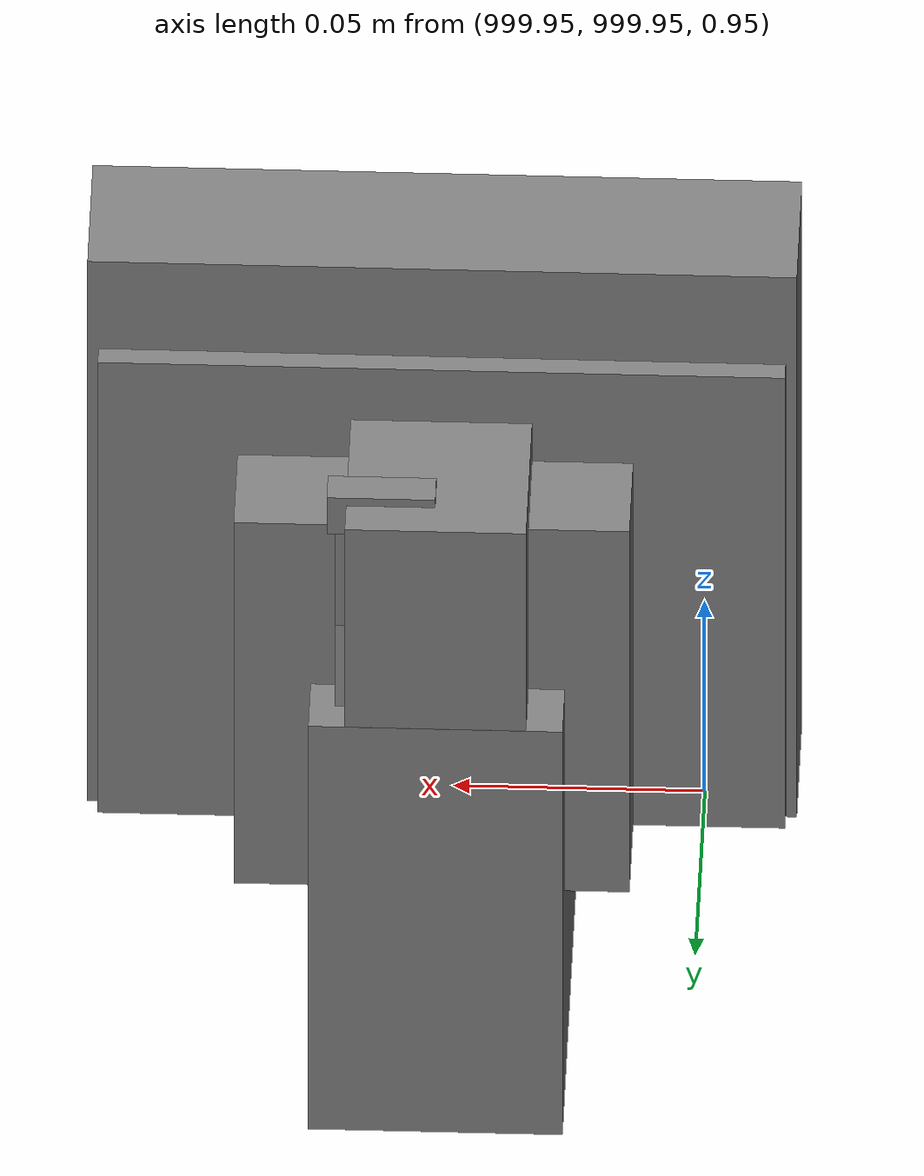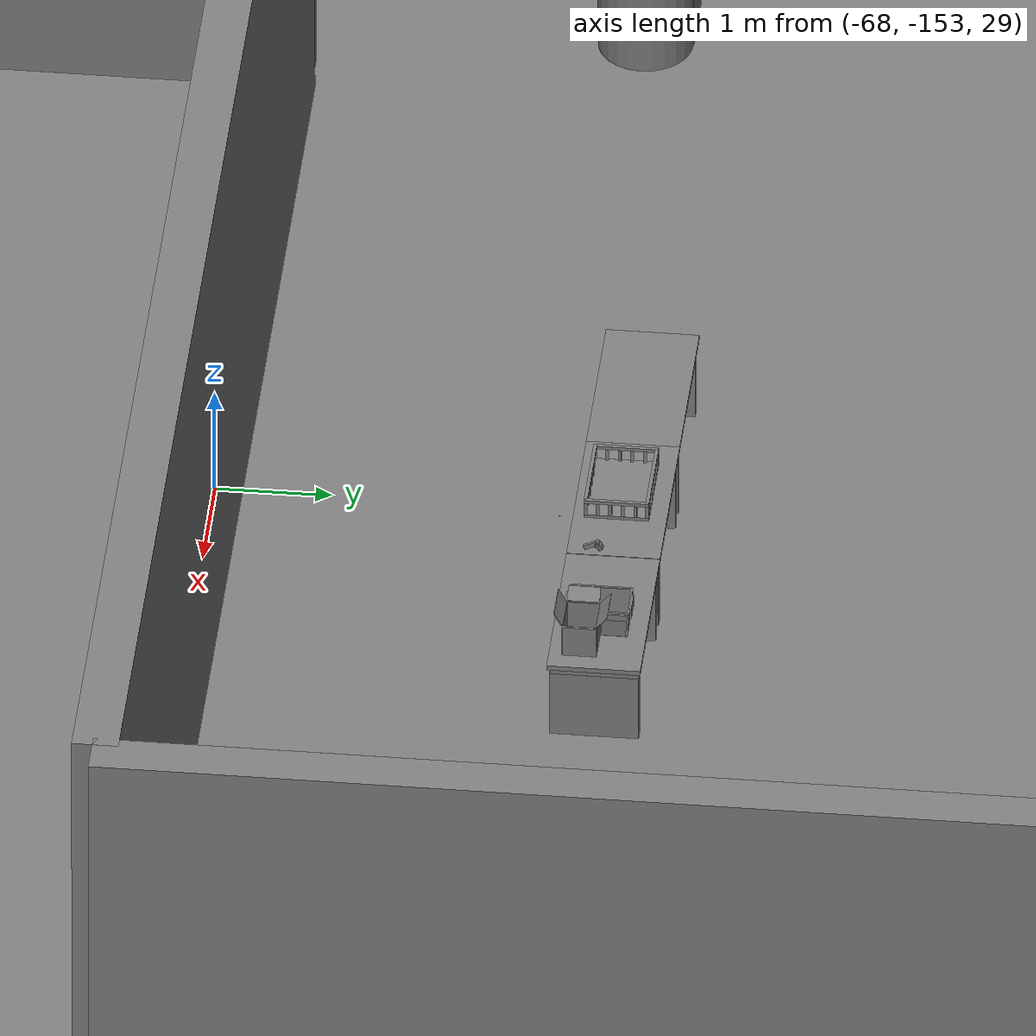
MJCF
<mujoco>
    <option gravity="0.000000000 0.000000000 -9.810000420" timestep="0.0049999999" integrator="implicitfast" density="1.225" viscosity="1.8000001e-05" noslip_iterations="10" iterations="100" sdf_iterations="50">
        <flag multiccd="disable"/>
    </option>
    <size memory="1000M"/>
    <compiler coordinate="local"/>
    <worldbody>
        <light cutoff="30" pos="0 1 1" dir="0 -1 -2"/>
        <light cutoff="30" pos="0 -1 1" dir="0 1 -2"/>
        <body pos="1000.000000000 1000.000000000 1.000000000" euler="0.000000000 0.000000000 180.000000000" name="openloong_gripper_2f85_fix_base_usda_cpu_fan">
            <geom contype="1" conaffinity="1" density="1000" type="box" material="" rgba="0.500000000 0.500000000 0.500000000 1.000000000" solimp="0.899999976 0.949999988 0.001000000" friction="1.000000000 0.005000000 0.000100000" solref="0.020000000 1.000000000" margin="0" condim="3" group="0" pos="0.000000000 0.000000000 0.070034981" quat="0.000000000 0.000000000 0.000000000 1.000000000" size="0.070700005 0.014699999 0.070700005" name="openloong_gripper_2f85_fix_base_usda_geom_84491E21_1206_49EF_BB8C_D9F92996E96F"/>
            <freejoint name="openloong_gripper_2f85_fix_base_usda_cpu_fan_joint"/>
            <site size="0.005000000 0.005000000 0.005000000" rgba="0.500000000 0.500000000 0.500000000 1.000000000" pos="0.000000000 0.000000000 0.000000000" quat="0.999961913 0.008726535 0.000000000 0.000000000" group="0" type="sphere" name="openloong_gripper_2f85_fix_base_usda_cpu_fancsite"/>
        </body>
        <body pos="1000.000000000 1000.000000000 1.000000000" euler="0.000000000 0.000000000 180.000000000" name="openloong_gripper_2f85_fix_base_usda_wifi_box">
            <geom contype="1" conaffinity="1" density="1000" type="box" material="" rgba="0.500000000 0.500000000 0.500000000 1.000000000" solimp="0.899999976 0.949999988 0.001000000" friction="1.000000000 0.005000000 0.000100000" solref="0.020000000 1.000000000" margin="0" condim="3" group="0" pos="0.000000000 0.000000000 0.058978677" quat="0.000000000 0.000000047 0.000000000 1.000000000" size="0.068499997 0.018999999 0.059000000" name="openloong_gripper_2f85_fix_base_usda_geom_760DCCB6_F774_4846_9051_29448F091372"/>
            <freejoint name="openloong_gripper_2f85_fix_base_usda_wifi_box_joint"/>
            <site size="0.005000000 0.005000000 0.005000000" rgba="0.500000000 0.500000000 0.500000000 1.000000000" pos="0.000000000 0.000000000 0.000000000" quat="0.999961913 0.008726500 0.000000000 0.000000000" group="0" type="sphere" name="openloong_gripper_2f85_fix_base_usda_wifi_boxsite"/>
        </body>
        <body pos="-65.968910217 -149.465362549 31.162914276" euler="-93.853073120 67.739219666 -73.724426270" mocap="true" name="spotlight1_SpotLight"/>
        <body pos="1000.000000000 999.999938965 1.000000000" euler="0.000000000 0.000000000 180.000000000" name="openloong_gripper_2f85_fix_base_usda_intelcore_i5">
            <geom contype="1" conaffinity="1" density="1000" type="box" material="" rgba="0.500000000 0.500000000 0.500000000 1.000000000" solimp="0.899999976 0.949999988 0.001000000" friction="1.000000000 0.005000000 0.000100000" solref="0.020000000 1.000000000" margin="0" condim="3" group="0" pos="0.000000000 0.000000000 0.051722717" quat="0.707106709 0.000000000 0.000000000 -0.707106769" size="0.052800000 0.018080002 0.052800000" name="openloong_gripper_2f85_fix_base_usda_geom_1EA8F319_FBCB_46DC_9E0D_A2A8D198FF00"/>
            <freejoint name="openloong_gripper_2f85_fix_base_usda_intelcore_i5_joint"/>
            <site size="0.005000000 0.005000000 0.005000000" rgba="0.500000000 0.500000000 0.500000000 1.000000000" pos="0.000000000 0.000000000 0.000000000" quat="0.999961913 0.008726534 0.000000000 0.000000000" group="0" type="sphere" name="openloong_gripper_2f85_fix_base_usda_intelcore_i5site"/>
        </body>
        <body pos="1000.000000000 1000.000000000 1.000000000" euler="0.000011953 0.000005123 -179.999984741" name="openloong_gripper_2f85_fix_base_usda_intel_box">
            <geom contype="1" conaffinity="1" density="1000" type="box" material="" rgba="0.500000000 0.500000000 0.500000000 1.000000000" solimp="0.899999976 0.949999988 0.001000000" friction="1.000000000 0.005000000 0.000100000" solref="0.020000000 1.000000000" margin="0" condim="3" group="0" pos="0.000000000 -0.000067139 0.000082284" quat="0.707106709 0.000000225 0.000000253 0.707106650" size="0.052800003 0.025300000 0.052800003" name="openloong_gripper_2f85_fix_base_usda_geom_31B99EDB_3A94_4DE7_ADF5_982B1B8E5A27"/>
            <freejoint name="openloong_gripper_2f85_fix_base_usda_intel_box_joint"/>
            <site size="0.005000000 0.005000000 0.005000000" rgba="0.500000000 0.500000000 0.500000000 1.000000000" pos="0.000000000 0.000000000 0.000000000" quat="0.999961913 0.008726500 0.000000000 0.000000000" group="0" type="sphere" name="openloong_gripper_2f85_fix_base_usda_intel_boxsite"/>
        </body>
        <body pos="-65.910957336 -149.415634155 31.169401169" euler="-67.666557312 56.074279785 127.361274719" mocap="true" name="spotlight3_SpotLight"/>
        <body pos="1000.000000000 1000.000000000 1.000000000" euler="0.000000000 0.000000000 180.000000000" name="openloong_gripper_2f85_fix_base_usda_battery_01">
            <geom contype="1" conaffinity="1" density="1000" type="box" material="" rgba="0.500000000 0.500000000 0.500000000 1.000000000" solimp="0.899999976 0.949999988 0.001000000" friction="1.000000000 0.005000000 0.000100000" solref="0.020000000 1.000000000" margin="0" condim="3" group="0" pos="-0.011123657 -0.041940309 0.101691343" quat="1.000000000 0.000000000 0.000000000 0.000000000" size="0.010800000 0.003375000 0.004725000" name="openloong_gripper_2f85_fix_base_usda_geom_CE754209_93A8_430D_A116_CF218ADF4E73"/>
            <geom contype="1" conaffinity="1" density="1000" type="box" material="" rgba="0.500000000 0.500000000 0.500000000 1.000000000" solimp="0.899999976 0.949999988 0.001000000" friction="1.000000000 0.005000000 0.000100000" solref="0.020000000 1.000000000" margin="0" condim="3" group="0" pos="-0.010876465 -0.044247437 0.047066893" quat="0.998702705 -0.050920475 0.000000000 0.000000000" size="0.009450001 0.002700000 0.024975000" name="openloong_gripper_2f85_fix_base_usda_geom_D187B319_C375_4417_A94E_FD23A6CAD38C"/>
            <geom contype="1" conaffinity="1" density="1000" type="box" material="" rgba="0.500000000 0.500000000 0.500000000 1.000000000" solimp="0.899999976 0.949999988 0.001000000" friction="1.000000000 0.005000000 0.000100000" solref="0.020000000 1.000000000" margin="0" condim="3" group="0" pos="-0.001235962 -0.000659180 0.047381196" quat="1.000000000 0.000000000 0.000000000 0.000000000" size="0.039420001 0.039150000 0.047250003" name="openloong_gripper_2f85_fix_base_usda_geom_E38165CF_3D99_4BC0_8148_59CADE0037F3"/>
            <geom contype="1" conaffinity="1" density="1000" type="box" material="" rgba="0.500000000 0.500000000 0.500000000 1.000000000" solimp="0.899999976 0.949999988 0.001000000" friction="1.000000000 0.005000000 0.000100000" solref="0.020000000 1.000000000" margin="0" condim="3" group="0" pos="-0.010876465 -0.039138794 0.009851727" quat="1.000000000 0.000000000 0.000000000 0.000000000" size="0.009450001 0.010800000 0.013500000" name="openloong_gripper_2f85_fix_base_usda_geom_FEE20187_BFCD_442B_AEFF_5AB13047CB3F"/>
            <geom contype="1" conaffinity="1" density="1000" type="box" material="" rgba="0.500000000 0.500000000 0.500000000 1.000000000" solimp="0.899999976 0.949999988 0.001000000" friction="1.000000000 0.005000000 0.000100000" solref="0.020000000 1.000000000" margin="0" condim="3" group="0" pos="-0.010876465 -0.041528322 0.071508206" quat="1.000000000 0.000000000 0.000000000 0.000000000" size="0.009450001 0.002700000 0.027000001" name="openloong_gripper_2f85_fix_base_usda_geom_6AE5EC0D_4E1A_48C4_A34B_EAC216A6F508"/>
            <freejoint name="openloong_gripper_2f85_fix_base_usda_battery_01_joint"/>
            <site size="0.005000000 0.005000000 0.005000000" rgba="0.500000000 0.500000000 0.500000000 1.000000000" pos="0.000000000 0.000000000 0.000000000" quat="0.999961913 0.008726500 0.000000000 0.000000000" group="0" type="sphere" name="openloong_gripper_2f85_fix_base_usda_battery_01site"/>
        </body>
        <body pos="-66.370697021 -149.797470093 31.163692474" euler="-64.574043274 57.141563416 12.032114029" mocap="true" name="spotlight4_SpotLight"/>
        <body pos="-64.866622925 -149.383972168 30.183746338" euler="89.999984741 89.999946594 0.000000000" name="openloong_gripper_2f85_fix_base_usda_bluebox_01">
            <geom contype="1" conaffinity="1" density="1000" type="box" material="" rgba="0.500000000 0.500000000 0.500000000 1.000000000" solimp="0.899999976 0.949999988 0.001000000" friction="1.000000000 0.005000000 0.000100000" solref="0.020000000 1.000000000" margin="0" condim="3" group="0" pos="0.276580811 0.187225342 0.000068665" quat="0.707106948 0.000077471 0.707106352 0.000077486" size="0.100000001 0.057999998 0.010000000" name="openloong_gripper_2f85_fix_base_usda_geom_E5F5A8E8_D462_4744_91B9_2B6DAFDAA105"/>
            <geom contype="1" conaffinity="1" density="1000" type="box" material="" rgba="0.500000000 0.500000000 0.500000000 1.000000000" solimp="0.899999976 0.949999988 0.001000000" friction="1.000000000 0.005000000 0.000100000" solref="0.020000000 1.000000000" margin="0" condim="3" group="0" pos="0.000000000 0.002883911 0.000000000" quat="0.999999881 0.000000000 0.000000000 0.000000000" size="0.254000008 0.003000000 0.172000006" name="openloong_gripper_2f85_fix_base_usda_geom_4E5F86AA_3F86_4A74_BFA7_2FA542CB7C5F"/>
            <geom contype="1" conaffinity="1" density="1000" type="box" material="" rgba="0.500000000 0.500000000 0.500000000 1.000000000" solimp="0.899999976 0.949999988 0.001000000" friction="1.000000000 0.005000000 0.000100000" solref="0.020000000 1.000000000" margin="0" condim="3" group="0" pos="0.000000000 0.124874115 0.173484802" quat="0.999796331 0.020176515 -0.000000015 0.000000030" size="0.259999990 0.119999997 0.007000000" name="openloong_gripper_2f85_fix_base_usda_geom_8B4D32A5_ACFB_4328_B509_5C98FF8BE5C4"/>
            <geom contype="1" conaffinity="1" density="1000" type="box" material="" rgba="0.500000000 0.500000000 0.500000000 1.000000000" solimp="0.899999976 0.949999988 0.001000000" friction="1.000000000 0.005000000 0.000100000" solref="0.020000000 1.000000000" margin="0" condim="3" group="0" pos="0.000000000 0.124874115 -0.173469543" quat="0.999796331 -0.020176545 -0.000000015 0.000000000" size="0.259999990 0.119999997 0.007000000" name="openloong_gripper_2f85_fix_base_usda_geom_6E327035_41E8_43CF_8F1B_3DBE5C357C44"/>
            <geom contype="1" conaffinity="1" density="1000" type="box" material="" rgba="0.500000000 0.500000000 0.500000000 1.000000000" solimp="0.899999976 0.949999988 0.001000000" friction="1.000000000 0.005000000 0.000100000" solref="0.020000000 1.000000000" margin="0" condim="3" group="0" pos="0.000000000 0.214008331 0.188980103" quat="0.999912977 0.013176724 0.000000015 0.000000000" size="0.259999990 0.029999999 0.012500000" name="openloong_gripper_2f85_fix_base_usda_geom_48C22B34_3118_44A2_8BBE_44EAEDE00E29"/>
            <geom contype="1" conaffinity="1" density="1000" type="box" material="" rgba="0.500000000 0.500000000 0.500000000 1.000000000" solimp="0.899999976 0.949999988 0.001000000" friction="1.000000000 0.005000000 0.000100000" solref="0.020000000 1.000000000" margin="0" condim="3" group="0" pos="-0.258361816 0.125289917 0.001876831" quat="0.702796936 -0.020792112 0.710783124 0.020769298" size="0.189999998 0.119999997 0.009000000" name="openloong_gripper_2f85_fix_base_usda_geom_A7CD7521_6355_413F_9450_62D4ACA51138"/>
            <geom contype="1" conaffinity="1" density="1000" type="box" material="" rgba="0.500000000 0.500000000 0.500000000 1.000000000" solimp="0.899999976 0.949999988 0.001000000" friction="1.000000000 0.005000000 0.000100000" solref="0.020000000 1.000000000" margin="0" condim="3" group="0" pos="0.000000000 0.214008331 -0.188980103" quat="0.999912977 -0.013176769 0.000000030 0.000000015" size="0.259999990 0.029999999 0.012500000" name="openloong_gripper_2f85_fix_base_usda_geom_BD3128ED_C48D_4418_8E31_840C4721F63D"/>
            <geom contype="1" conaffinity="1" density="1000" type="box" material="" rgba="0.500000000 0.500000000 0.500000000 1.000000000" solimp="0.899999976 0.949999988 0.001000000" friction="1.000000000 0.005000000 0.000100000" solref="0.020000000 1.000000000" margin="0" condim="3" group="0" pos="-0.276611328 0.187225342 0.000068665" quat="0.707106650 0.000077441 0.707106709 0.000077456" size="0.100000001 0.057999998 0.010000000" name="openloong_gripper_2f85_fix_base_usda_geom_8A123D7C_D522_4EF9_89C6_CBA11F7A23CD"/>
            <geom contype="1" conaffinity="1" density="1000" type="box" material="" rgba="0.500000000 0.500000000 0.500000000 1.000000000" solimp="0.899999976 0.949999988 0.001000000" friction="1.000000000 0.005000000 0.000100000" solref="0.020000000 1.000000000" margin="0" condim="3" group="0" pos="0.258331299 0.125289917 0.001876831" quat="0.702851415 0.018856421 0.710823774 -0.019329369" size="0.189999998 0.119999997 0.009000000" name="openloong_gripper_2f85_fix_base_usda_geom_34E43417_35FA_4635_9830_2637E29E2C9C"/>
            <freejoint name="openloong_gripper_2f85_fix_base_usda_bluebox_01_joint"/>
            <site size="0.005000000 0.005000000 0.005000000" rgba="0.500000000 0.500000000 0.500000000 1.000000000" pos="0.000000000 0.000000000 0.000000000" quat="0.999961913 0.008726534 0.000000000 0.000000000" group="0" type="sphere" name="openloong_gripper_2f85_fix_base_usda_bluebox_01site"/>
        </body>
        <body pos="-64.496299744 -149.491867065 30.235729218" euler="0.000000000 0.000000000 89.999946594" name="openloong_gripper_2f85_fix_base_usda_cardboardbox_01">
            <geom contype="1" conaffinity="1" density="1000" type="box" material="" rgba="0.500000000 0.500000000 0.500000000 1.000000000" solimp="0.899999976 0.949999988 0.001000000" friction="1.000000000 0.005000000 0.000100000" solref="0.020000000 1.000000000" margin="0" condim="3" group="0" pos="-0.003166199 -0.004086494 0.005052090" quat="1.000000000 0.000000000 0.000000000 0.000000000" size="0.142499998 0.177500010 0.005000000" name="openloong_gripper_2f85_fix_base_usda_geom_9BB7B9A8_9358_4C6C_864A_7670F914DD8F"/>
            <geom contype="1" conaffinity="1" density="1000" type="box" material="" rgba="0.500000000 0.500000000 0.500000000 1.000000000" solimp="0.899999976 0.949999988 0.001000000" friction="1.000000000 0.005000000 0.000100000" solref="0.020000000 1.000000000" margin="0" condim="3" group="0" pos="-0.003166199 0.170316696 0.150570869" quat="1.000000000 0.000000000 0.000000000 0.000000000" size="0.142499998 0.005000000 0.149999991" name="openloong_gripper_2f85_fix_base_usda_geom_D2DD7420_A357_4DA8_BAD7_D8822A635597"/>
            <geom contype="1" conaffinity="1" density="1000" type="box" material="" rgba="0.500000000 0.500000000 0.500000000 1.000000000" solimp="0.899999976 0.949999988 0.001000000" friction="1.000000000 0.005000000 0.000100000" solref="0.020000000 1.000000000" margin="0" condim="3" group="0" pos="-0.147399902 -0.005307198 0.150570869" quat="1.000000000 0.000000000 0.000000000 0.000000000" size="0.005000000 0.177500010 0.149999991" name="openloong_gripper_2f85_fix_base_usda_geom_8FDAF8C7_D4AC_414C_8FBB_B529405D1083"/>
            <geom contype="1" conaffinity="1" density="1000" type="box" material="" rgba="0.500000000 0.500000000 0.500000000 1.000000000" solimp="0.899999976 0.949999988 0.001000000" friction="1.000000000 0.005000000 0.000100000" solref="0.020000000 1.000000000" margin="0" condim="3" group="0" pos="0.140275955 -0.005307198 0.150570869" quat="1.000000000 0.000000000 0.000000000 0.000000000" size="0.005000000 0.177500010 0.149999991" name="openloong_gripper_2f85_fix_base_usda_geom_620E7B57_5E97_4046_B9B2_520C4E8E342F"/>
            <geom contype="1" conaffinity="1" density="1000" type="box" material="" rgba="0.500000000 0.500000000 0.500000000 1.000000000" solimp="0.899999976 0.949999988 0.001000000" friction="1.000000000 0.005000000 0.000100000" solref="0.020000000 1.000000000" margin="0" condim="3" group="0" pos="-0.003166199 -0.181550980 0.150570869" quat="1.000000000 0.000000000 0.000000000 0.000000000" size="0.142499998 0.005000000 0.149999991" name="openloong_gripper_2f85_fix_base_usda_geom_304022CF_5473_480D_A588_80A5DA43A862"/>
            <freejoint name="openloong_gripper_2f85_fix_base_usda_cardboardbox_01_joint"/>
            <site size="0.005000000 0.005000000 0.005000000" rgba="0.500000000 0.500000000 0.500000000 1.000000000" pos="0.000000000 0.000000000 0.000000000" quat="0.999961913 0.008726535 0.000000000 0.000000000" group="0" type="sphere" name="openloong_gripper_2f85_fix_base_usda_site_81C48C47_0305_4823_9DBF_D81F820BA299"/>
            <body pos="0.139160156 -0.004048347 0.301930904" euler="-179.999954224 49.383502960 179.999954224" name="openloong_gripper_2f85_fix_base_usda_A1_006">
                <geom contype="1" conaffinity="1" density="1000" type="box" material="" rgba="0.500000000 0.500000000 0.500000000 1.000000000" solimp="0.899999976 0.949999988 0.001000000" friction="1.000000000 0.005000000 0.000100000" solref="0.020000000 1.000000000" margin="0" condim="3" group="0" pos="-0.071587563 0.000009537 0.001745224" quat="0.999999881 0.000000000 0.000000000 0.000000000" size="0.071249999 0.179999992 0.002500000" name="openloong_gripper_2f85_fix_base_usda_geom_BE7AC5BD_3909_4BF9_A7B9_62D4AD15EFBB"/>
                <joint armature="0" stiffness="0.07" damping="0.0099999998" axis="0.000000 1.000000 0.000000" type="hinge" name="openloong_gripper_2f85_fix_base_usda_A1_006"/>
            </body>
            <body pos="-0.145902634 -0.004086494 0.301938057" euler="-180.000000000 -60.000011444 -180.000000000" name="openloong_gripper_2f85_fix_base_usda_A2_006">
                <geom contype="1" conaffinity="1" density="1000" type="box" material="" rgba="0.500000000 0.500000000 0.500000000 1.000000000" solimp="0.899999976 0.949999988 0.001000000" friction="1.000000000 0.005000000 0.000100000" solref="0.020000000 1.000000000" margin="0" condim="3" group="0" pos="0.071268082 0.000009537 0.002717972" quat="0.000002921 0.000000000 -0.000000030 0.999999881" size="0.071249999 0.179999992 0.002500000" name="openloong_gripper_2f85_fix_base_usda_geom_D24F8C55_0E32_4BF3_BE9B_DEF24A711F50"/>
                <joint armature="0" stiffness="0.07" damping="0.0099999998" axis="0.000000 1.000000 0.000000" type="hinge" name="openloong_gripper_2f85_fix_base_usda_A2_006"/>
            </body>
            <body pos="-0.003385544 0.175991058 0.301930904" euler="-125.858116150 -0.000004561 0.000002331" name="openloong_gripper_2f85_fix_base_usda_B2_006">
                <geom contype="1" conaffinity="1" density="1000" type="box" material="" rgba="0.500000000 0.500000000 0.500000000 1.000000000" solimp="0.899999976 0.949999988 0.001000000" friction="1.000000000 0.005000000 0.000100000" solref="0.020000000 1.000000000" margin="0" condim="3" group="0" pos="0.000009537 -0.070939064 -0.002470016" quat="0.999614120 0.027776197 -0.000000015 0.000000030" size="0.137500003 0.064999998 0.005000000" name="openloong_gripper_2f85_fix_base_usda_geom_EBBE5413_B524_4C48_8DC7_7EC77E0C57F5"/>
                <joint armature="0" stiffness="0.07" damping="0.0099999998" axis="1.000000 0.000000 0.000000" type="hinge" name="openloong_gripper_2f85_fix_base_usda_B2_006"/>
            </body>
            <body pos="-0.003385544 -0.184140205 0.301938057" euler="147.805557251 0.000000000 0.000000000" name="openloong_gripper_2f85_fix_base_usda_B1_006">
                <geom contype="1" conaffinity="1" density="1000" type="box" material="" rgba="0.500000000 0.500000000 0.500000000 1.000000000" solimp="0.899999976 0.949999988 0.001000000" friction="1.000000000 0.005000000 0.000100000" solref="0.020000000 1.000000000" margin="0" condim="3" group="0" pos="-0.000028610 0.070202351 -0.002703667" quat="0.999614179 -0.027776167 0.000000000 0.000000000" size="0.137500003 0.064999998 0.005000000" name="openloong_gripper_2f85_fix_base_usda_geom_D21E7351_68AF_435C_933C_2068F58637B3"/>
                <joint armature="0" stiffness="0.07" damping="0.0099999998" axis="1.000000 0.000000 0.000000" type="hinge" name="openloong_gripper_2f85_fix_base_usda_B1_006"/>
            </body>
        </body>
        <body pos="-65.882858276 -149.481979370 30.229999542" euler="-64.487716675 0.000000000 0.000000000" name="openloong_gripper_2f85_fix_base_usda_Barcode">
            <geom contype="1" conaffinity="1" density="1000" type="box" material="" rgba="0.500000000 0.500000000 0.500000000 1.000000000" solimp="0.899999976 0.949999988 0.001000000" friction="1.000000000 0.005000000 0.000100000" solref="0.020000000 1.000000000" margin="0" condim="3" group="0" pos="0.000000000 0.013038635 0.001419067" quat="0.000000000 0.000000000 0.000000000 1.000000119" size="0.034000002 0.010000000 0.017999999" name="openloong_gripper_2f85_fix_base_usda_geom_C6BE7ADC_2D83_4700_A037_95163F2C2A47"/>
            <geom contype="1" conaffinity="1" density="1000" type="box" material="" rgba="0.500000000 0.500000000 0.500000000 1.000000000" solimp="0.899999976 0.949999988 0.001000000" friction="1.000000000 0.005000000 0.000100000" solref="0.020000000 1.000000000" margin="0" condim="3" group="0" pos="0.000000000 -0.035301208 -0.007095337" quat="0.000000000 0.000000000 -0.043619365 0.999048233" size="0.028999999 0.010000000 0.020000000" name="openloong_gripper_2f85_fix_base_usda_geom_9F0638DE_7AE3_4DE2_BF40_7DF43692A094"/>
            <geom contype="1" conaffinity="1" density="1000" type="box" material="" rgba="0.500000000 0.500000000 0.500000000 1.000000000" solimp="0.899999976 0.949999988 0.001000000" friction="1.000000000 0.005000000 0.000100000" solref="0.020000000 1.000000000" margin="0" condim="3" group="0" pos="0.000000000 -0.043411255 -0.011749268" quat="0.922262907 0.386563420 0.000000000 0.000000000" size="0.026000001 0.010000000 0.020000000" name="openloong_gripper_2f85_fix_base_usda_geom_42FBEC63_D2AC_4990_9F43_AE78653D3E8D"/>
            <geom contype="1" conaffinity="1" density="1000" type="box" material="" rgba="0.500000000 0.500000000 0.500000000 1.000000000" solimp="0.899999976 0.949999988 0.001000000" friction="1.000000000 0.005000000 0.000100000" solref="0.020000000 1.000000000" margin="0" condim="3" group="0" pos="0.000000000 -0.016967773 -0.031860352" quat="0.000000000 0.000000000 0.000000000 1.000000119" size="0.008000000 0.010000000 0.013000000" name="openloong_gripper_2f85_fix_base_usda_geom_EDD9A8DC_BED1_4200_B44C_AD2A349D2193"/>
            <geom contype="1" conaffinity="1" density="1000" type="box" material="" rgba="0.500000000 0.500000000 0.500000000 1.000000000" solimp="0.899999976 0.949999988 0.001000000" friction="1.000000000 0.005000000 0.000100000" solref="0.020000000 1.000000000" margin="0" condim="3" group="0" pos="0.000000000 -0.001869202 0.000312805" quat="0.953716993 0.300705761 0.000000000 0.000000000" size="0.032000002 0.010000000 0.018999999" name="openloong_gripper_2f85_fix_base_usda_geom_EB553363_A373_4163_89C1_23B74478F193"/>
            <geom contype="1" conaffinity="1" density="1000" type="box" material="" rgba="0.500000000 0.500000000 0.500000000 1.000000000" solimp="0.899999976 0.949999988 0.001000000" friction="1.000000000 0.005000000 0.000100000" solref="0.020000000 1.000000000" margin="0" condim="3" group="0" pos="0.000000000 -0.019531250 -0.003173828" quat="0.953716993 0.300705761 0.000000000 0.000000000" size="0.030999999 0.010000000 0.020000000" name="openloong_gripper_2f85_fix_base_usda_geom_85B8DD4D_78B3_4807_9128_CBA7AF9485CC"/>
            <geom contype="1" conaffinity="1" density="1000" type="box" material="" rgba="0.500000000 0.500000000 0.500000000 1.000000000" solimp="0.899999976 0.949999988 0.001000000" friction="1.000000000 0.005000000 0.000100000" solref="0.020000000 1.000000000" margin="0" condim="3" group="0" pos="0.000000000 -0.035301208 -0.007095337" quat="0.953716993 0.300705761 0.000000000 0.000000000" size="0.028999999 0.010000000 0.020000000" name="openloong_gripper_2f85_fix_base_usda_geom_1F469946_0A02_46CB_8E0D_306B714AA020"/>
            <geom contype="1" conaffinity="1" density="1000" type="box" material="" rgba="0.500000000 0.500000000 0.500000000 1.000000000" solimp="0.899999976 0.949999988 0.001000000" friction="1.000000000 0.005000000 0.000100000" solref="0.020000000 1.000000000" margin="0" condim="3" group="0" pos="0.000000000 -0.042617798 -0.071121216" quat="0.000000000 0.000000000 0.000000000 1.000000119" size="0.013000000 0.021000000 0.059999999" name="openloong_gripper_2f85_fix_base_usda_geom_92EBE9EC_F3C9_44EB_86C5_1A8A9483B1E2"/>
            <freejoint name="openloong_gripper_2f85_fix_base_usda_Barcode_joint"/>
            <site size="0.005000000 0.005000000 0.005000000" rgba="0.500000000 0.500000000 0.500000000 1.000000000" pos="0.000000000 0.000000000 0.000000000" quat="1.000000000 0.000000000 0.000000000 0.000000000" group="0" type="sphere" name="openloong_gripper_2f85_fix_base_usda_Barcode_site"/>
        </body>
        <body pos="-66.745018005 -149.392349243 30.184000015" euler="0.000000000 0.000000000 89.999946594" name="[22330596350415]_Basket_01">
            <geom contype="1" conaffinity="1" density="1000" type="box" material="" rgba="0.500000000 0.500000000 0.500000000 1.000000000" solimp="0.899999976 0.949999988 0.001000000" friction="1.000000000 0.005000000 0.000100000" solref="0.020000000 1.000000000" margin="0" condim="3" group="0" pos="-0.052425385 0.389207840 0.089787483" quat="0.707107008 0.000000000 0.000000000 0.707106411" size="0.014249999 0.014249999 0.059999999" name="[22330596350415]_geom_F2AE8BB3_5CA3_4C72_AEBB_4918EE93745F"/>
            <geom contype="1" conaffinity="1" density="1000" type="box" material="" rgba="0.500000000 0.500000000 0.500000000 1.000000000" solimp="0.899999976 0.949999988 0.001000000" friction="1.000000000 0.005000000 0.000100000" solref="0.020000000 1.000000000" margin="0" condim="3" group="0" pos="0.264015198 -0.133043289 0.089787483" quat="0.707107008 0.000000000 0.000000000 0.707106411" size="0.014249999 0.014249999 0.059999999" name="[22330596350415]_geom_DB157A1D_B734_474F_8121_9547887172AD"/>
            <geom contype="1" conaffinity="1" density="1000" type="box" material="" rgba="0.500000000 0.500000000 0.500000000 1.000000000" solimp="0.899999976 0.949999988 0.001000000" friction="1.000000000 0.005000000 0.000100000" solref="0.020000000 1.000000000" margin="0" condim="3" group="0" pos="-0.264015198 -0.265548706 0.089793205" quat="0.707107008 0.000000000 0.000000000 0.707106411" size="0.014249999 0.014249999 0.059999999" name="[22330596350415]_geom_009787CD_65ED_4197_84D4_FD381D683BF6"/>
            <geom contype="1" conaffinity="1" density="1000" type="box" material="" rgba="0.500000000 0.500000000 0.500000000 1.000000000" solimp="0.899999976 0.949999988 0.001000000" friction="1.000000000 0.005000000 0.000100000" solref="0.020000000 1.000000000" margin="0" condim="3" group="0" pos="-0.160263062 -0.389322281 0.089793205" quat="0.707107008 0.000000000 0.000000000 0.707106411" size="0.014249999 0.014249999 0.059999999" name="[22330596350415]_geom_99C73DBD_A0AA_4EDE_B3CB_791ECFFBF877"/>
            <geom contype="1" conaffinity="1" density="1000" type="box" material="" rgba="0.500000000 0.500000000 0.500000000 1.000000000" solimp="0.899999976 0.949999988 0.001000000" friction="1.000000000 0.005000000 0.000100000" solref="0.020000000 1.000000000" margin="0" condim="3" group="0" pos="0.162265778 -0.389322281 0.089787483" quat="0.707107008 0.000000000 0.000000000 0.707106411" size="0.014249999 0.014249999 0.059999999" name="[22330596350415]_geom_910BB7CC_AF69_4D83_8001_F82D64A5EF12"/>
            <geom contype="1" conaffinity="1" density="1000" type="box" material="" rgba="0.500000000 0.500000000 0.500000000 1.000000000" solimp="0.899999976 0.949999988 0.001000000" friction="1.000000000 0.005000000 0.000100000" solref="0.020000000 1.000000000" margin="0" condim="3" group="0" pos="0.264015198 0.389207840 0.089787483" quat="0.707107008 0.000000000 0.000000000 0.707106411" size="0.014249999 0.014249999 0.059999999" name="[22330596350415]_geom_A96061EA_E535_4439_B031_40FD7ADD9613"/>
            <geom contype="1" conaffinity="1" density="1000" type="box" material="" rgba="0.500000000 0.500000000 0.500000000 1.000000000" solimp="0.899999976 0.949999988 0.001000000" friction="1.000000000 0.005000000 0.000100000" solref="0.020000000 1.000000000" margin="0" condim="3" group="0" pos="-0.264015198 -0.133043289 0.089793205" quat="0.707107008 0.000000000 0.000000000 0.707106411" size="0.014249999 0.014249999 0.059999999" name="[22330596350415]_geom_62CACE34_8348_4AA0_8E00_5085BFAA6801"/>
            <geom contype="1" conaffinity="1" density="1000" type="box" material="" rgba="0.500000000 0.500000000 0.500000000 1.000000000" solimp="0.899999976 0.949999988 0.001000000" friction="1.000000000 0.005000000 0.000100000" solref="0.020000000 1.000000000" margin="0" condim="3" group="0" pos="-0.264026642 0.269256592 0.089793205" quat="0.707107008 0.000000000 0.000000000 0.707106411" size="0.014249999 0.014249999 0.059999999" name="[22330596350415]_geom_3E2F3070_47BA_4655_A521_6F30A5F7EFB4"/>
            <geom contype="1" conaffinity="1" density="1000" type="box" material="" rgba="0.500000000 0.500000000 0.500000000 1.000000000" solimp="0.899999976 0.949999988 0.001000000" friction="1.000000000 0.005000000 0.000100000" solref="0.020000000 1.000000000" margin="0" condim="3" group="0" pos="0.054462433 0.389207840 0.089787483" quat="0.707107008 0.000000000 0.000000000 0.707106411" size="0.014249999 0.014249999 0.059999999" name="[22330596350415]_geom_E9EE191A_6D75_4E29_91C3_5023FF3C4C86"/>
            <geom contype="1" conaffinity="1" density="1000" type="box" material="" rgba="0.500000000 0.500000000 0.500000000 1.000000000" solimp="0.899999976 0.949999988 0.001000000" friction="1.000000000 0.005000000 0.000100000" solref="0.020000000 1.000000000" margin="0" condim="3" group="0" pos="0.054462433 -0.389322281 0.089787483" quat="0.707107008 0.000000000 0.000000000 0.707106411" size="0.014249999 0.014249999 0.059999999" name="[22330596350415]_geom_E786D048_8CDA_4E49_BEEE_4BFD3602B15E"/>
            <geom contype="1" conaffinity="1" density="1000" type="box" material="" rgba="0.500000000 0.500000000 0.500000000 1.000000000" solimp="0.899999976 0.949999988 0.001000000" friction="1.000000000 0.005000000 0.000100000" solref="0.020000000 1.000000000" margin="0" condim="3" group="0" pos="0.264015198 0.269256592 0.089793205" quat="0.707107008 0.000000000 0.000000000 0.707106411" size="0.014249999 0.014249999 0.059999999" name="[22330596350415]_geom_988B487B_BCD3_436E_8C22_F59E3090E628"/>
            <geom contype="1" conaffinity="1" density="1000" type="box" material="" rgba="0.500000000 0.500000000 0.500000000 1.000000000" solimp="0.899999976 0.949999988 0.001000000" friction="1.000000000 0.005000000 0.000100000" solref="0.020000000 1.000000000" margin="0" condim="3" group="0" pos="0.264015198 -0.389322281 0.089787483" quat="0.707107008 0.000000000 0.000000000 0.707106411" size="0.014249999 0.014249999 0.059999999" name="[22330596350415]_geom_D2788B6C_F7D0_44B7_A9F3_1BBA07AB1968"/>
            <geom contype="1" conaffinity="1" density="1000" type="box" material="" rgba="0.500000000 0.500000000 0.500000000 1.000000000" solimp="0.899999976 0.949999988 0.001000000" friction="1.000000000 0.005000000 0.000100000" solref="0.020000000 1.000000000" margin="0" condim="3" group="0" pos="0.000000000 0.000000000 0.015998840" quat="0.707107008 0.000000000 0.000000000 0.707106411" size="0.403499991 0.279000014 0.015750000" name="[22330596350415]_geom_CCAF7E88_1A8E_4908_AD8A_A66DE8FBFC3E"/>
            <geom contype="1" conaffinity="1" density="1000" type="box" material="" rgba="0.500000000 0.500000000 0.500000000 1.000000000" solimp="0.899999976 0.949999988 0.001000000" friction="1.000000000 0.005000000 0.000100000" solref="0.020000000 1.000000000" margin="0" condim="3" group="0" pos="0.000000000 -0.389476776 0.163619041" quat="0.707107008 0.000000000 0.000000000 0.707106411" size="0.015000000 0.277500004 0.015750000" name="[22330596350415]_geom_046DB812_409F_462D_A0B1_A85C5574840A"/>
            <geom contype="1" conaffinity="1" density="1000" type="box" material="" rgba="0.500000000 0.500000000 0.500000000 1.000000000" solimp="0.899999976 0.949999988 0.001000000" friction="1.000000000 0.005000000 0.000100000" solref="0.020000000 1.000000000" margin="0" condim="3" group="0" pos="0.162265778 0.389207840 0.089787483" quat="0.707107008 0.000000000 0.000000000 0.707106411" size="0.014249999 0.014249999 0.059999999" name="[22330596350415]_geom_86EB12BD_4873_49A0_A634_B80660BE67D0"/>
            <geom contype="1" conaffinity="1" density="1000" type="box" material="" rgba="0.500000000 0.500000000 0.500000000 1.000000000" solimp="0.899999976 0.949999988 0.001000000" friction="1.000000000 0.005000000 0.000100000" solref="0.020000000 1.000000000" margin="0" condim="3" group="0" pos="0.000000000 0.389471054 0.163619041" quat="0.707107008 0.000000000 0.000000000 0.707106411" size="0.015000000 0.277500004 0.015750000" name="[22330596350415]_geom_BA52F231_01FF_49F8_B996_BA618B54F22F"/>
            <geom contype="1" conaffinity="1" density="1000" type="box" material="" rgba="0.500000000 0.500000000 0.500000000 1.000000000" solimp="0.899999976 0.949999988 0.001000000" friction="1.000000000 0.005000000 0.000100000" solref="0.020000000 1.000000000" margin="0" condim="3" group="0" pos="-0.263511658 0.000000000 0.163619041" quat="0.707107008 0.000000000 0.000000000 0.707106411" size="0.403499991 0.015000000 0.015750000" name="[22330596350415]_geom_23CD9B3B_5D04_470A_B346_B948D29589C0"/>
            <geom contype="1" conaffinity="1" density="1000" type="box" material="" rgba="0.500000000 0.500000000 0.500000000 1.000000000" solimp="0.899999976 0.949999988 0.001000000" friction="1.000000000 0.005000000 0.000100000" solref="0.020000000 1.000000000" margin="0" condim="3" group="0" pos="-0.264015198 0.141334534 0.089793205" quat="0.707107008 0.000000000 0.000000000 0.707106411" size="0.014249999 0.014249999 0.059999999" name="[22330596350415]_geom_40BBEBC6_2981_462C_83FF_6780E4DD15EA"/>
            <geom contype="1" conaffinity="1" density="1000" type="box" material="" rgba="0.500000000 0.500000000 0.500000000 1.000000000" solimp="0.899999976 0.949999988 0.001000000" friction="1.000000000 0.005000000 0.000100000" solref="0.020000000 1.000000000" margin="0" condim="3" group="0" pos="0.264015198 -0.265548706 0.089787483" quat="0.707107008 0.000000000 0.000000000 0.707106411" size="0.014249999 0.014249999 0.059999999" name="[22330596350415]_geom_97ADE902_D89C_4F80_B361_B5DA2A89AA10"/>
            <geom contype="1" conaffinity="1" density="1000" type="box" material="" rgba="0.500000000 0.500000000 0.500000000 1.000000000" solimp="0.899999976 0.949999988 0.001000000" friction="1.000000000 0.005000000 0.000100000" solref="0.020000000 1.000000000" margin="0" condim="3" group="0" pos="-0.160263062 0.389207840 0.089787483" quat="0.707107008 0.000000000 0.000000000 0.707106411" size="0.014249999 0.014249999 0.059999999" name="[22330596350415]_geom_792636C6_307E_4582_87D0_82943C993E72"/>
            <geom contype="1" conaffinity="1" density="1000" type="box" material="" rgba="0.500000000 0.500000000 0.500000000 1.000000000" solimp="0.899999976 0.949999988 0.001000000" friction="1.000000000 0.005000000 0.000100000" solref="0.020000000 1.000000000" margin="0" condim="3" group="0" pos="-0.052425385 -0.389322281 0.089787483" quat="0.707107008 0.000000000 0.000000000 0.707106411" size="0.014249999 0.014249999 0.059999999" name="[22330596350415]_geom_0EDF0DCB_C80C_439B_9771_32F9C0905C8F"/>
            <geom contype="1" conaffinity="1" density="1000" type="box" material="" rgba="0.500000000 0.500000000 0.500000000 1.000000000" solimp="0.899999976 0.949999988 0.001000000" friction="1.000000000 0.005000000 0.000100000" solref="0.020000000 1.000000000" margin="0" condim="3" group="0" pos="-0.264026642 -0.389322281 0.089793205" quat="0.707107008 0.000000000 0.000000000 0.707106411" size="0.014249999 0.014249999 0.059999999" name="[22330596350415]_geom_44CEF956_00BB_450C_8113_1C777FF4006D"/>
            <geom contype="1" conaffinity="1" density="1000" type="box" material="" rgba="0.500000000 0.500000000 0.500000000 1.000000000" solimp="0.899999976 0.949999988 0.001000000" friction="1.000000000 0.005000000 0.000100000" solref="0.020000000 1.000000000" margin="0" condim="3" group="0" pos="0.264015198 0.141334534 0.089787483" quat="0.707107008 0.000000000 0.000000000 0.707106411" size="0.014249999 0.014249999 0.059999999" name="[22330596350415]_geom_68BF5B04_FE34_4916_89E1_30CA3B431AF1"/>
            <geom contype="1" conaffinity="1" density="1000" type="box" material="" rgba="0.500000000 0.500000000 0.500000000 1.000000000" solimp="0.899999976 0.949999988 0.001000000" friction="1.000000000 0.005000000 0.000100000" solref="0.020000000 1.000000000" margin="0" condim="3" group="0" pos="-0.264015198 0.389207840 0.089793205" quat="0.707107008 0.000000000 0.000000000 0.707106411" size="0.014249999 0.014249999 0.059999999" name="[22330596350415]_geom_893C1BA6_B174_42E8_9AF0_52238CB6D705"/>
            <geom contype="1" conaffinity="1" density="1000" type="box" material="" rgba="0.500000000 0.500000000 0.500000000 1.000000000" solimp="0.899999976 0.949999988 0.001000000" friction="1.000000000 0.005000000 0.000100000" solref="0.020000000 1.000000000" margin="0" condim="3" group="0" pos="0.264015198 0.004480362 0.089787483" quat="0.707107008 0.000000000 0.000000000 0.707106411" size="0.014249999 0.014249999 0.059999999" name="[22330596350415]_geom_A8D55E45_1917_4F98_9EA9_37EEFB6A7994"/>
            <geom contype="1" conaffinity="1" density="1000" type="box" material="" rgba="0.500000000 0.500000000 0.500000000 1.000000000" solimp="0.899999976 0.949999988 0.001000000" friction="1.000000000 0.005000000 0.000100000" solref="0.020000000 1.000000000" margin="0" condim="3" group="0" pos="0.263694763 -0.000011444 0.163619041" quat="0.707107008 0.000000000 0.000000000 0.707106411" size="0.403499991 0.015000000 0.015750000" name="[22330596350415]_geom_AC6CB30D_3498_4AC5_B656_F7929B4D430F"/>
            <geom contype="1" conaffinity="1" density="1000" type="box" material="" rgba="0.500000000 0.500000000 0.500000000 1.000000000" solimp="0.899999976 0.949999988 0.001000000" friction="1.000000000 0.005000000 0.000100000" solref="0.020000000 1.000000000" margin="0" condim="3" group="0" pos="-0.264015198 0.004480362 0.089793205" quat="0.707107008 0.000000000 0.000000000 0.707106411" size="0.014249999 0.014249999 0.059999999" name="[22330596350415]_geom_701D32E7_DD3B_4ECD_B6A6_B8EA13ECB8DE"/>
            <freejoint name="[22330596350415]_joint_94345A7B_C3CB_4AC8_AD22_86B85C3E324A"/>
        </body>
        <body pos="0.000000000 0.000000000 0.000000000" euler="0.000000000 0.000000000 0.000000000" name="Static Objects_Static Objects">
            <geom contype="1" conaffinity="1" density="1000" type="box" material="" rgba="0.500000000 0.500000000 0.500000000 1.000000000" solimp="0.899999976 0.949999988 0.001000000" friction="1.000000000 0.005000000 0.000100000" solref="0.020000000 1.000000000" margin="0" condim="3" group="0" pos="-67.544113159 -149.365814209 29.727830887" quat="0.500000417 0.499999970 0.499999553 0.499999970" size="0.381000012 0.319999993 0.041000001" name="Static Objects_geom_85352852_97F3_4BD8_A51B_E835F104F03E"/>
            <geom contype="1" conaffinity="1" density="1000" type="box" material="" rgba="0.500000000 0.500000000 0.500000000 1.000000000" solimp="0.899999976 0.949999988 0.001000000" friction="1.000000000 0.005000000 0.000100000" solref="0.020000000 1.000000000" margin="0" condim="3" group="0" pos="-68.239501953 -149.365814209 30.086868286" quat="0.500000417 0.499999970 0.499999553 0.499999970" size="0.370999992 0.039500002 0.745000005" name="Static Objects_geom_CD1F6E9F_F757_4B1D_AA7D_AAC737CA4C3C"/>
            <geom contype="1" conaffinity="1" density="1000" type="box" material="" rgba="0.500000000 0.500000000 0.500000000 1.000000000" solimp="0.899999976 0.949999988 0.001000000" friction="1.000000000 0.005000000 0.000100000" solref="0.020000000 1.000000000" margin="0" condim="3" group="0" pos="-68.239501953 -149.365814209 30.147235870" quat="0.500000417 0.499999970 0.499999553 0.499999970" size="0.400000006 0.022000000 0.800000012" name="Static Objects_geom_DB97404F_D1A0_4200_BD46_98923C70E7B0"/>
            <geom contype="1" conaffinity="1" density="1000" type="box" material="" rgba="0.500000000 0.500000000 0.500000000 1.000000000" solimp="0.899999976 0.949999988 0.001000000" friction="1.000000000 0.005000000 0.000100000" solref="0.020000000 1.000000000" margin="0" condim="3" group="0" pos="-68.934890747 -149.365814209 29.727830887" quat="0.500000417 0.499999970 0.499999553 0.499999970" size="0.381000012 0.319999993 0.041000001" name="Static Objects_geom_360A34CD_991E_487C_B542_53905DB5AA50"/>
            <geom contype="1" conaffinity="1" density="1000" type="box" material="" rgba="0.500000000 0.500000000 0.500000000 1.000000000" solimp="0.899999976 0.949999988 0.001000000" friction="1.000000000 0.005000000 0.000100000" solref="0.020000000 1.000000000" margin="0" condim="3" group="0" pos="-68.239501953 -149.365814209 29.561563492" quat="0.500000417 0.499999970 0.499999553 0.499999970" size="0.020000000 0.022000000 0.660000026" name="Static Objects_geom_9E77A929_FAAB_4BAF_98CC_24F2B9D63CF4"/>
            <geom contype="1" conaffinity="1" density="1000" type="box" material="" rgba="0.500000000 0.500000000 0.500000000 1.000000000" solimp="0.899999976 0.949999988 0.001000000" friction="1.000000000 0.005000000 0.000100000" solref="0.020000000 1.000000000" margin="0" condim="3" group="0" pos="-65.945671082 -149.365814209 29.727830887" quat="0.500000417 0.499999970 0.499999553 0.499999970" size="0.381000012 0.319999993 0.041000001" name="Static Objects_geom_D206AFC7_CC85_4072_8CAD_7C0945931CD3"/>
            <geom contype="1" conaffinity="1" density="1000" type="box" material="" rgba="0.500000000 0.500000000 0.500000000 1.000000000" solimp="0.899999976 0.949999988 0.001000000" friction="1.000000000 0.005000000 0.000100000" solref="0.020000000 1.000000000" margin="0" condim="3" group="0" pos="-66.641059875 -149.365814209 30.086868286" quat="0.500000417 0.499999970 0.499999553 0.499999970" size="0.370999992 0.039500002 0.745000005" name="Static Objects_geom_039EB603_3CD5_4521_AFEF_482DB225E430"/>
            <geom contype="1" conaffinity="1" density="1000" type="box" material="" rgba="0.500000000 0.500000000 0.500000000 1.000000000" solimp="0.899999976 0.949999988 0.001000000" friction="1.000000000 0.005000000 0.000100000" solref="0.020000000 1.000000000" margin="0" condim="3" group="0" pos="-66.641059875 -149.365814209 30.147235870" quat="0.500000417 0.499999970 0.499999553 0.499999970" size="0.400000006 0.022000000 0.800000012" name="Static Objects_geom_86D1E47E_A282_4595_902C_FD7353AC5ED1"/>
            <geom contype="1" conaffinity="1" density="1000" type="box" material="" rgba="0.500000000 0.500000000 0.500000000 1.000000000" solimp="0.899999976 0.949999988 0.001000000" friction="1.000000000 0.005000000 0.000100000" solref="0.020000000 1.000000000" margin="0" condim="3" group="0" pos="-67.336448669 -149.365814209 29.727830887" quat="0.500000417 0.499999970 0.499999553 0.499999970" size="0.381000012 0.319999993 0.041000001" name="Static Objects_geom_074C08E3_7FB1_4345_9A69_7F2F98973448"/>
            <geom contype="1" conaffinity="1" density="1000" type="box" material="" rgba="0.500000000 0.500000000 0.500000000 1.000000000" solimp="0.899999976 0.949999988 0.001000000" friction="1.000000000 0.005000000 0.000100000" solref="0.020000000 1.000000000" margin="0" condim="3" group="0" pos="-66.641059875 -149.365814209 29.561563492" quat="0.500000417 0.499999970 0.499999553 0.499999970" size="0.020000000 0.022000000 0.660000026" name="Static Objects_geom_D0256036_F43C_4148_B9CA_6BCF1FB52F66"/>
            <geom contype="1" conaffinity="1" density="1000" type="box" material="" rgba="0.500000000 0.500000000 0.500000000 1.000000000" solimp="0.899999976 0.949999988 0.001000000" friction="1.000000000 0.005000000 0.000100000" solref="0.020000000 1.000000000" margin="0" condim="3" group="0" pos="-64.338577271 -149.365814209 29.727830887" quat="0.500000417 0.499999970 0.499999553 0.499999970" size="0.381000012 0.319999993 0.041000001" name="Static Objects_geom_2F7CE8E9_1C5A_4CD1_B7C0_1B7A7470AE5E"/>
            <geom contype="1" conaffinity="1" density="1000" type="box" material="" rgba="0.500000000 0.500000000 0.500000000 1.000000000" solimp="0.899999976 0.949999988 0.001000000" friction="1.000000000 0.005000000 0.000100000" solref="0.020000000 1.000000000" margin="0" condim="3" group="0" pos="-65.033966064 -149.365814209 30.086868286" quat="0.500000417 0.499999970 0.499999553 0.499999970" size="0.370999992 0.039500002 0.745000005" name="Static Objects_geom_63E50E57_A39F_4642_B157_BDEF9F7B67D6"/>
            <geom contype="1" conaffinity="1" density="1000" type="box" material="" rgba="0.500000000 0.500000000 0.500000000 1.000000000" solimp="0.899999976 0.949999988 0.001000000" friction="1.000000000 0.005000000 0.000100000" solref="0.020000000 1.000000000" margin="0" condim="3" group="0" pos="-65.033966064 -149.365814209 30.147235870" quat="0.500000417 0.499999970 0.499999553 0.499999970" size="0.400000006 0.022000000 0.800000012" name="Static Objects_geom_C131C191_AB0A_45AC_B4AB_FAF10457BD50"/>
            <geom contype="1" conaffinity="1" density="1000" type="box" material="" rgba="0.500000000 0.500000000 0.500000000 1.000000000" solimp="0.899999976 0.949999988 0.001000000" friction="1.000000000 0.005000000 0.000100000" solref="0.020000000 1.000000000" margin="0" condim="3" group="0" pos="-65.729354858 -149.365814209 29.727830887" quat="0.500000417 0.499999970 0.499999553 0.499999970" size="0.381000012 0.319999993 0.041000001" name="Static Objects_geom_CE70177F_F5A7_4E89_9A80_16BB9C669DF7"/>
            <geom contype="1" conaffinity="1" density="1000" type="box" material="" rgba="0.500000000 0.500000000 0.500000000 1.000000000" solimp="0.899999976 0.949999988 0.001000000" friction="1.000000000 0.005000000 0.000100000" solref="0.020000000 1.000000000" margin="0" condim="3" group="0" pos="-65.033966064 -149.365814209 29.561563492" quat="0.500000417 0.499999970 0.499999553 0.499999970" size="0.020000000 0.022000000 0.660000026" name="Static Objects_geom_096735E7_D38E_4163_9798_B7E4DB2EC657"/>
            <geom contype="1" conaffinity="1" density="1000" type="box" material="" rgba="0.500000000 0.500000000 0.500000000 1.000000000" solimp="0.899999976 0.949999988 0.001000000" friction="1.000000000 0.005000000 0.000100000" solref="0.020000000 1.000000000" margin="0" condim="3" group="0" pos="-61.754566193 -137.853729248 33.906845093" quat="0.707107067 0.000000000 0.000000000 0.707106471" size="0.759999990 0.759999990 4.500000000" name="Static Objects_geom_BF5C8D70_C4DC_4FDD_8EBC_4B038DC0A8AD"/>
            <geom contype="1" conaffinity="1" density="1000" type="box" material="" rgba="0.500000000 0.500000000 0.500000000 1.000000000" solimp="0.899999976 0.949999988 0.001000000" friction="1.000000000 0.005000000 0.000100000" solref="0.020000000 1.000000000" margin="0" condim="3" group="0" pos="-57.511135101 -144.927108765 31.707921982" quat="1.000000000 0.000000000 0.000000000 0.000000000" size="0.200000003 8.000000000 2.299999952" name="Static Objects_geom_8F1F24B5_9072_4EEC_B63C_DA64FEE06A50"/>
            <geom contype="1" conaffinity="1" density="1000" type="box" material="" rgba="0.500000000 0.500000000 0.500000000 1.000000000" solimp="0.899999976 0.949999988 0.001000000" friction="1.000000000 0.005000000 0.000100000" solref="0.020000000 1.000000000" margin="0" condim="3" group="0" pos="-80.517646790 -157.574050903 31.688196182" quat="0.707107067 0.000000000 0.000000000 0.707106471" size="0.600000024 0.600000024 2.299999952" name="Static Objects_geom_2C1B61B2_1821_48D3_A131_AC67C1C38729"/>
            <geom contype="1" conaffinity="1" density="1000" type="box" material="" rgba="0.500000000 0.500000000 0.500000000 1.000000000" solimp="0.899999976 0.949999988 0.001000000" friction="1.000000000 0.005000000 0.000100000" solref="0.020000000 1.000000000" margin="0" condim="3" group="0" pos="-80.711044312 -147.414932251 31.666158676" quat="1.000000000 0.000000000 0.000000000 0.000000000" size="0.200000003 10.000000000 2.299999952" name="Static Objects_geom_8D2A8642_E605_4BC9_BBFB_FED0B472DBD3"/>
            <geom contype="1" conaffinity="1" density="1000" type="box" material="" rgba="0.500000000 0.500000000 0.500000000 1.000000000" solimp="0.899999976 0.949999988 0.001000000" friction="1.000000000 0.005000000 0.000100000" solref="0.020000000 1.000000000" margin="0" condim="3" group="0" pos="-57.687217712 -137.434692383 31.688196182" quat="0.707107067 0.000000000 0.000000000 0.707106471" size="0.600000024 0.600000024 2.299999952" name="Static Objects_geom_BA84AEA3_4B21_4CCA_A6B7_E56EE77E5B12"/>
            <geom contype="1" conaffinity="1" density="1000" type="box" material="" rgba="0.500000000 0.500000000 0.500000000 1.000000000" solimp="0.899999976 0.949999988 0.001000000" friction="1.000000000 0.005000000 0.000100000" solref="0.020000000 1.000000000" margin="0" condim="3" group="0" pos="-69.537033081 -140.263229370 31.714921951" quat="0.707107067 0.000000000 0.000000000 0.707106471" size="0.759999990 4.500000000 2.299999952" name="Static Objects_geom_9662F767_F340_4999_A1AE_3736F0E1B6D4"/>
            <geom contype="1" conaffinity="1" density="1000" type="box" material="" rgba="0.500000000 0.500000000 0.500000000 1.000000000" solimp="0.899999976 0.949999988 0.001000000" friction="1.000000000 0.005000000 0.000100000" solref="0.020000000 1.000000000" margin="0" condim="3" group="0" pos="-80.073638916 -137.853713989 33.906845093" quat="0.707107067 0.000000000 0.000000000 0.707106471" size="0.759999990 0.759999990 4.500000000" name="Static Objects_geom_FD23052D_F8EF_4039_B366_BFDD815E5EB0"/>
            <geom contype="1" conaffinity="1" density="1000" type="box" material="" rgba="0.500000000 0.500000000 0.500000000 1.000000000" solimp="0.899999976 0.949999988 0.001000000" friction="1.000000000 0.005000000 0.000100000" solref="0.020000000 1.000000000" margin="0" condim="3" group="0" pos="-73.406707764 -155.734664917 31.707921982" quat="1.000000000 0.000000000 0.000000000 0.000000000" size="0.200000003 3.000000000 2.299999952" name="Static Objects_geom_FD021DF1_F018_4EE3_A8A5_541C11804A9F"/>
            <geom contype="1" conaffinity="1" density="1000" type="box" material="" rgba="0.500000000 0.500000000 0.500000000 1.000000000" solimp="0.899999976 0.949999988 0.001000000" friction="1.000000000 0.005000000 0.000100000" solref="0.020000000 1.000000000" margin="0" condim="3" group="0" pos="-68.497543335 -137.448257446 31.707921982" quat="0.707107067 0.000000000 0.000000000 0.707106471" size="0.200000003 14.000000000 2.299999952" name="Static Objects_geom_BB024EF0_2BBC_4656_B85B_FAA436082D26"/>
            <geom contype="1" conaffinity="1" density="1000" type="cylinder" material="" rgba="0.500000000 0.500000000 0.500000000 1.000000000" solimp="0.899999976 0.949999988 0.001000000" friction="1.000000000 0.005000000 0.000100000" solref="0.020000000 1.000000000" margin="0" condim="3" group="0" pos="-68.868522644 -142.134506226 31.711090088" quat="0.707107067 0.000000000 0.000000000 0.707106471" size="0.509999990 2.299999952 1.000000000" name="Static Objects_geom_A01B72A3_0B85_47D3_A867_076EAD96D95A"/>
            <geom contype="1" conaffinity="1" density="1000" type="plane" material="" rgba="0.500000000 0.500000000 0.500000000 1.000000000" solimp="0.899999976 0.949999988 0.001000000" friction="1.000000000 0.005000000 0.000100000" solref="0.020000000 1.000000000" margin="0" condim="3" group="0" pos="-72.873703003 -147.131927490 29.409669876" quat="1.000000000 0.000000000 0.000000000 0.000000000" size="18.000000000 14.000000000 1.000000000" name="Static Objects_geom_83257B81_690D_426C_9B1E_B0DBEAF18D9C"/>
            <geom contype="1" conaffinity="1" density="1000" type="box" material="" rgba="0.500000000 0.500000000 0.500000000 1.000000000" solimp="0.899999976 0.949999988 0.001000000" friction="1.000000000 0.005000000 0.000100000" solref="0.020000000 1.000000000" margin="0" condim="3" group="0" pos="-79.943580627 -157.782272339 31.707921982" quat="0.707107067 0.000000000 0.000000000 0.707106471" size="0.200000003 7.000000000 2.299999952" name="Static Objects_geom_0769BF3F_8675_4979_BAD7_4116EA01377C"/>
            <geom contype="1" conaffinity="1" density="1000" type="box" material="" rgba="0.500000000 0.500000000 0.500000000 1.000000000" solimp="0.899999976 0.949999988 0.001000000" friction="1.000000000 0.005000000 0.000100000" solref="0.020000000 1.000000000" margin="0" condim="3" group="0" pos="-65.421028137 -152.903442383 31.707921982" quat="0.707107067 0.000000000 0.000000000 0.707106471" size="0.200000003 7.800000191 2.299999952" name="Static Objects_geom_3B77466E_5A89_40E6_A13D_087984ABDF19"/>
            <geom contype="1" conaffinity="1" density="1000" type="box" material="" rgba="0.500000000 0.500000000 0.500000000 1.000000000" solimp="0.899999976 0.949999988 0.001000000" friction="1.000000000 0.005000000 0.000100000" solref="0.020000000 1.000000000" margin="0" condim="3" group="0" pos="-74.776908875 -149.964416504 31.688196182" quat="1.000000000 0.000000000 0.000000000 0.000000000" size="0.600000024 0.409999996 2.299999952" name="Static Objects_geom_2C8044D8_5203_4A6D_90B9_91DC1BD7F726"/>
            <geom contype="1" conaffinity="1" density="1000" type="cylinder" material="" rgba="0.500000000 0.500000000 0.500000000 1.000000000" solimp="0.899999976 0.949999988 0.001000000" friction="1.000000000 0.005000000 0.000100000" solref="0.020000000 1.000000000" margin="0" condim="3" group="0" pos="-60.161884308 -142.134506226 31.711090088" quat="0.707107067 0.000000000 0.000000000 0.707106471" size="0.509999990 2.299999952 1.000000000" name="Static Objects_geom_B64E0194_819E_4208_8723_AD294CAB89F1"/>
            <geom contype="1" conaffinity="1" density="1000" type="cylinder" material="" rgba="0.500000000 0.500000000 0.500000000 1.000000000" solimp="0.899999976 0.949999988 0.001000000" friction="1.000000000 0.005000000 0.000100000" solref="0.020000000 1.000000000" margin="0" condim="3" group="0" pos="-75.382453918 -149.963455200 31.711090088" quat="0.707107067 0.000000000 0.000000000 0.707106471" size="0.409999996 2.299999952 1.000000000" name="Static Objects_geom_A24702AB_34D8_4291_9A08_CC69E7F2E67A"/>
            <geom contype="1" conaffinity="1" density="1000" type="cylinder" material="" rgba="0.500000000 0.500000000 0.500000000 1.000000000" solimp="0.899999976 0.949999988 0.001000000" friction="1.000000000 0.005000000 0.000100000" solref="0.020000000 1.000000000" margin="0" condim="3" group="0" pos="-74.154960632 -149.963455200 31.711090088" quat="0.707107067 0.000000000 0.000000000 0.707106471" size="0.409999996 2.299999952 1.000000000" name="Static Objects_geom_7650A70F_A8C9_4D06_B81A_6B1C51CF070A"/>
            <geom contype="1" conaffinity="1" density="1000" type="cylinder" material="" rgba="0.500000000 0.500000000 0.500000000 1.000000000" solimp="0.899999976 0.949999988 0.001000000" friction="1.000000000 0.005000000 0.000100000" solref="0.020000000 1.000000000" margin="0" condim="3" group="0" pos="-77.566612244 -142.134506226 31.711090088" quat="0.707107067 0.000000000 0.000000000 0.707106471" size="0.509999990 2.299999952 1.000000000" name="Static Objects_geom_E98E683E_080B_4435_88A6_36F9B5594435"/>
        </body>
        <body pos="-66.291030884 -149.869689941 29.018842697" euler="0.000000000 0.000000000 89.999946594" mocap="true" name="openloong_gripper_2f85_fix_base_usda_leftHandMocap"/>
        <body pos="-66.291030884 -149.869689941 29.018842697" euler="0.000000000 0.000000000 89.999946594" mocap="true" name="openloong_gripper_2f85_fix_base_usda_rightHandMocap"/>
        <body pos="-66.291030884 -149.869689941 30.218843460" euler="0.000000000 0.000000000 89.999946594" name="openloong_gripper_2f85_fix_base_usda_base_link">
            <geom contype="1" conaffinity="1" density="1000" type="mesh" material="" rgba="0.783999979 0.783999979 0.783999979 1.000000000" solimp="0.899999976 0.949999988 0.001000000" friction="1.000000000 0.005000000 0.000100000" solref="0.020000000 1.000000000" margin="0" condim="3" group="3" mesh="base_link" pos="0.000000000 0.000000000 0.000000000" quat="1.000000000 0.000000000 0.000000000 0.000000000" size="1.000000000 1.000000000 1.000000000" name="openloong_gripper_2f85_fix_base_usda__geom_7_84189354_A1C8_4D1E_8E97_A69C5A0D6305"/>
            <site size="0.005000000 0.005000000 0.005000000" rgba="0.500000000 0.500000000 0.500000000 1.000000000" pos="0.000000000 0.000000000 0.000000000" quat="1.000000000 0.000000000 0.000000000 0.000000000" group="0" type="sphere" name="openloong_gripper_2f85_fix_base_usda_imu"/>
            <inertial mass="22.447001" pos="-0.005664100 -0.001336700 0.238289997" diaginertia="0.374352545 0.277180195 0.220617250" quat="0.999247074 0.035235517 -0.015086859 0.006023135"/>
            <body pos="0.000000000 0.000000000 0.299997330" euler="0.000000000 0.000000000 0.000000000" name="openloong_gripper_2f85_fix_base_usda_dummy_body">
                <geom contype="1" conaffinity="1" density="1000" type="sphere" material="" rgba="0.783999979 0.783999979 0.783999979 1.000000000" solimp="0.899999976 0.949999988 0.001000000" friction="1.000000000 0.005000000 0.000100000" solref="0.020000000 1.000000000" margin="0" condim="3" group="3" pos="0.000000000 0.000000000 0.000000000" quat="1.000000000 0.000000000 0.000000000 0.000000000" size="0.010000000 0.000000000 0.000000000" name="openloong_gripper_2f85_fix_base_usda__geom_8_3D00A13A_7BFB_4816_A893_9B2B08BD8401"/>
                <joint armature="0.0099999998" stiffness="0" damping="0.1" axis="0.000000 0.000000 1.000000" type="hinge" name="openloong_gripper_2f85_fix_base_usda_dummy_joint"/>
                <site size="0.010000000 0.005000000 0.005000000" rgba="0.500000000 0.500000000 0.500000000 1.000000000" pos="0.000000000 0.000000000 0.000000000" quat="1.000000000 0.000000000 0.000000000 0.000000000" group="3" type="sphere" name="openloong_gripper_2f85_fix_base_usda_dummy_site"/>
            </body>
            <body pos="0.009002686 0.000000000 0.406400681" euler="0.000000000 0.000000000 0.000000000" name="openloong_gripper_2f85_fix_base_usda_Link_head_yaw">
                <geom contype="1" conaffinity="1" density="1000" type="mesh" material="" rgba="0.783999979 0.783999979 0.783999979 1.000000000" solimp="0.899999976 0.949999988 0.001000000" friction="1.000000000 0.005000000 0.000100000" solref="0.020000000 1.000000000" margin="0" condim="3" group="3" mesh="Link_head_yaw" pos="0.000000000 0.000000000 0.000000000" quat="1.000000000 0.000000000 0.000000000 0.000000000" size="1.000000000 1.000000000 1.000000000" name="openloong_gripper_2f85_fix_base_usda__geom_10_8A8F61A7_9941_4875_A51D_9F6473C755ED"/>
                <inertial mass="0.84249002" pos="0.000000000 -0.002081400 0.044801001" diaginertia="0.000700588 0.000629000 0.000553812" quat="0.706933022 -0.015675601 0.015677100 0.706933022"/>
                <body pos="0.000000000 -0.034599304 0.048500061" euler="0.000000000 0.000000000 0.000000000" name="openloong_gripper_2f85_fix_base_usda_Link_head_pitch">
                    <geom contype="1" conaffinity="1" density="1000" type="mesh" material="" rgba="0.783999979 0.783999979 0.783999979 1.000000000" solimp="0.899999976 0.949999988 0.001000000" friction="1.000000000 0.005000000 0.000100000" solref="0.020000000 1.000000000" margin="0" condim="3" group="3" mesh="Link_head_pitch" pos="0.000000000 0.000000000 0.000000000" quat="1.000000000 0.000000000 0.000000000 0.000000000" size="1.000000000 1.000000000 1.000000000" name="openloong_gripper_2f85_fix_base_usda__geom_12_150B3584_94B0_4E5D_823B_0E04134A4B47"/>
                    <inertial mass="1.3943" pos="0.020569000 0.033004001 0.125000000" diaginertia="0.006381400 0.006289940 0.004481460" quat="0.973390222 0.008406822 0.228157058 0.019624906"/>
                    <body pos="0.000000000 0.029998779 0.000000000" euler="0.000000000 0.000000000 0.000000000" name="openloong_gripper_2f85_fix_base_usda_neck_center_body">
                        <site size="0.010000000 0.005000000 0.005000000" rgba="0.500000000 0.500000000 0.500000000 1.000000000" pos="0.000000000 0.000000000 0.000000000" quat="1.000000000 0.000000000 0.000000000 0.000000000" group="3" type="sphere" name="openloong_gripper_2f85_fix_base_usda_neck_center_site"/>
                        <body pos="0.020004272 0.000000000 0.149999619" euler="-0.000002229 39.998176575 -90.000205994" name="openloong_gripper_2f85_fix_base_usda_camera_head">
                            <site size="0.010000000 0.005000000 0.005000000" rgba="0.500000000 0.500000000 0.500000000 1.000000000" pos="0.000000000 0.000000000 0.000000000" quat="1.000000000 0.000000000 0.000000000 0.000000000" group="3" type="sphere" name="openloong_gripper_2f85_fix_base_usda_camera_head_site"/>
                        </body>
                    </body>
                </body>
            </body>
            <body pos="0.003997803 -0.161598206 0.392200470" euler="0.000000000 0.000000000 0.000000000" name="openloong_gripper_2f85_fix_base_usda_Link_arm_r_01">
                <geom contype="1" conaffinity="1" density="1000" type="mesh" material="" rgba="0.783999979 0.783999979 0.783999979 1.000000000" solimp="0.899999976 0.949999988 0.001000000" friction="1.000000000 0.005000000 0.000100000" solref="0.020000000 1.000000000" margin="0" condim="3" group="3" mesh="Link_arm_r_01" pos="0.000000000 0.000000000 0.000000000" quat="1.000000000 0.000000000 0.000000000 0.000000000" size="1.000000000 1.000000000 1.000000000" name="openloong_gripper_2f85_fix_base_usda__geom_14_B3416E99_BE8C_46F7_9BA1_0AB04144A333"/>
                <joint armature="0.0099999998" stiffness="0" damping="1" axis="0.000000 -1.000000 0.000000" limited="true" range="-170.000015259 170.000015259" type="hinge" name="openloong_gripper_2f85_fix_base_usda_J_arm_r_01"/>
                <inertial mass="0.75641" pos="0.004494600 -0.038293999 -0.000001874" diaginertia="0.000842990 0.000803050 0.000587120" quat="-0.000163502 0.707098067 0.000812463 0.707115054"/>
                <body pos="-0.041992188 -0.041000366 0.000000000" euler="0.000000000 0.000000000 0.000000000" name="openloong_gripper_2f85_fix_base_usda_Link_arm_r_02">
                    <geom contype="1" conaffinity="1" density="1000" type="mesh" material="" rgba="0.783999979 0.783999979 0.783999979 1.000000000" solimp="0.899999976 0.949999988 0.001000000" friction="1.000000000 0.005000000 0.000100000" solref="0.020000000 1.000000000" margin="0" condim="3" group="3" mesh="Link_arm_r_02" pos="0.000000000 0.000000000 0.000000000" quat="1.000000000 0.000000000 0.000000000 0.000000000" size="1.000000000 1.000000000 1.000000000" name="openloong_gripper_2f85_fix_base_usda__geom_16_30831090_60B9_4C3F_A388_C0510AB519B6"/>
                    <joint armature="0.0099999998" stiffness="0" damping="1" axis="-1.000000 0.000000 0.000000" limited="true" range="-105.000244141 105.000244141" type="hinge" name="openloong_gripper_2f85_fix_base_usda_J_arm_r_02"/>
                    <inertial mass="0.98500001" pos="0.041999999 -0.067430697 0.000000000" diaginertia="0.002262690 0.001730990 0.001154020" quat="0.500000000 0.500000000 -0.500000000 0.500000000"/>
                    <body pos="0.041992188 -0.122596741 0.000000000" euler="0.000000000 0.000000000 0.000000000" name="openloong_gripper_2f85_fix_base_usda_Link_arm_r_03">
                        <geom contype="1" conaffinity="1" density="1000" type="mesh" material="" rgba="0.783999979 0.783999979 0.783999979 1.000000000" solimp="0.899999976 0.949999988 0.001000000" friction="1.000000000 0.005000000 0.000100000" solref="0.020000000 1.000000000" margin="0" condim="3" group="3" mesh="Link_arm_r_03" pos="0.000000000 0.000000000 0.000000000" quat="1.000000000 0.000000000 0.000000000 0.000000000" size="1.000000000 1.000000000 1.000000000" name="openloong_gripper_2f85_fix_base_usda__geom_18_2AFBCF1B_3288_469A_AFD7_8BF189BCAD38"/>
                        <joint armature="0.0099999998" stiffness="0" damping="1" axis="0.000000 -1.000000 0.000000" limited="true" range="-170.000015259 170.000015259" type="hinge" name="openloong_gripper_2f85_fix_base_usda_J_arm_r_03"/>
                        <inertial mass="0.95899999" pos="-0.001413580 -0.164663002 0.020757901" diaginertia="0.002101340 0.002064590 0.000754802" quat="0.560480952 0.454391927 -0.443732947 0.531497955"/>
                        <body pos="0.035293579 -0.177406311 0.023998260" euler="0.000000000 0.000000000 0.000000000" name="openloong_gripper_2f85_fix_base_usda_Link_arm_r_04">
                            <geom contype="1" conaffinity="1" density="1000" type="mesh" material="" rgba="0.783999979 0.783999979 0.783999979 1.000000000" solimp="0.899999976 0.949999988 0.001000000" friction="1.000000000 0.005000000 0.000100000" solref="0.020000000 1.000000000" margin="0" condim="3" group="3" mesh="Link_arm_r_04" pos="0.000000000 0.000000000 0.000000000" quat="1.000000000 0.000000000 0.000000000 0.000000000" size="1.000000000 1.000000000 1.000000000" name="openloong_gripper_2f85_fix_base_usda__geom_20_22E2BD27_B251_4251_934D_970CC4140459"/>
                            <joint armature="0.0099999998" stiffness="0" damping="1" axis="-1.000000 0.000000 0.000000" limited="true" range="0.000000000 170.000015259" type="hinge" name="openloong_gripper_2f85_fix_base_usda_J_arm_r_04"/>
                            <inertial mass="0.60000002" pos="-0.038727000 -0.060766999 -0.021003000" diaginertia="0.001092610 0.000712422 0.000645102" quat="0.327701002 0.632602990 -0.467366993 0.523443997"/>
                            <body pos="-0.035293579 -0.103492737 -0.023998260" euler="0.000000000 0.000000000 0.000000000" name="openloong_gripper_2f85_fix_base_usda_Link_arm_r_05">
                                <geom contype="1" conaffinity="1" density="1000" type="mesh" material="" rgba="0.783999979 0.783999979 0.783999979 1.000000000" solimp="0.899999976 0.949999988 0.001000000" friction="1.000000000 0.005000000 0.000100000" solref="0.020000000 1.000000000" margin="0" condim="3" group="3" mesh="Link_arm_r_05" pos="0.000000000 0.000000000 0.000000000" quat="1.000000000 0.000000000 0.000000000 0.000000000" size="1.000000000 1.000000000 1.000000000" name="openloong_gripper_2f85_fix_base_usda__geom_22_5016C4D8_55F5_40A8_825B_EBD4CC3A4E72"/>
                                <joint armature="0.0099999998" stiffness="0" damping="1" axis="0.000000 -1.000000 0.000000" limited="true" range="-170.000015259 170.000015259" type="hinge" name="openloong_gripper_2f85_fix_base_usda_J_arm_r_05"/>
                                <inertial mass="0.68976003" pos="0.000032712 -0.068658002 -0.000111780" diaginertia="0.002522510 0.002411100 0.000448695" quat="0.707660973 0.706543028 -0.002603360 0.002470550"/>
                                <body pos="-0.026489258 -0.196502686 0.000000000" euler="0.000000000 0.000000000 0.000000000" name="openloong_gripper_2f85_fix_base_usda_Link_arm_r_06">
                                    <geom contype="1" conaffinity="1" density="1000" type="mesh" material="" rgba="0.783999979 0.783999979 0.783999979 1.000000000" solimp="0.899999976 0.949999988 0.001000000" friction="1.000000000 0.005000000 0.000100000" solref="0.020000000 1.000000000" margin="0" condim="3" group="3" mesh="Link_arm_r_06" pos="0.000000000 0.000000000 0.000000000" quat="1.000000000 0.000000000 0.000000000 0.000000000" size="1.000000000 1.000000000 1.000000000" name="openloong_gripper_2f85_fix_base_usda__geom_24_2B28DCED_2B71_4DA7_ABCD_DF32FF6F2AEF"/>
                                    <joint armature="0.0099999998" stiffness="0" damping="1" axis="1.000000 0.000000 0.000000" limited="true" range="-105.000244141 105.000244141" type="hinge" name="openloong_gripper_2f85_fix_base_usda_J_arm_r_06"/>
                                    <inertial mass="0.28" pos="0.026078001 -0.000000896 0.001663700" diaginertia="0.000156930 0.000145601 0.000104979" quat="0.707080841 0.001851080 0.001883810 0.707127810"/>
                                    <body pos="0.026489258 0.000000000 0.031799316" euler="0.000000000 0.000000000 0.000000000" name="openloong_gripper_2f85_fix_base_usda_Link_arm_r_07">
                                        <geom contype="1" conaffinity="1" density="1000" type="mesh" material="" rgba="0.783999979 0.783999979 0.783999979 1.000000000" solimp="0.899999976 0.949999988 0.001000000" friction="1.000000000 0.005000000 0.000100000" solref="0.020000000 1.000000000" margin="0" condim="3" group="3" mesh="Link_arm_r_07" pos="0.000000000 0.000000000 0.000000000" quat="1.000000000 0.000000000 0.000000000 0.000000000" size="1.000000000 1.000000000 1.000000000" name="openloong_gripper_2f85_fix_base_usda__geom_26_A03336FD_FA28_4F32_ACDC_EC687F757E2F"/>
                                        <joint armature="0.0099999998" stiffness="0" damping="1" axis="0.000000 0.000000 1.000000" limited="true" range="-60.000133514 60.000133514" type="hinge" name="openloong_gripper_2f85_fix_base_usda_J_arm_r_07"/>
                                        <inertial mass="0.61353999" pos="-0.007859000 -0.158170000 -0.027736001" diaginertia="0.003037610 0.002570910 0.000729379" quat="0.427542925 0.443532884 -0.553093910 0.560867906"/>
                                        <body pos="0.000000000 0.286994934 -0.270000458" euler="150.000350952 -0.000001649 -0.000000442" name="openloong_gripper_2f85_fix_base_usda_camera_wrist_r">
                                            <site size="0.010000000 0.005000000 0.005000000" rgba="0.500000000 0.500000000 0.500000000 1.000000000" pos="0.000000000 0.000000000 0.000000000" quat="1.000000000 0.000000000 0.000000000 0.000000000" group="3" type="sphere" name="openloong_gripper_2f85_fix_base_usda_camera_wrist_r_site"/>
                                        </body>
                                        <body pos="0.000000000 -0.220008850 -0.033002853" euler="0.000000000 0.000000000 179.999969482" name="openloong_gripper_2f85_fix_base_usda_ee_center_body_r">
                                            <site size="0.010000000 0.005000000 0.005000000" rgba="0.500000000 0.500000000 0.500000000 1.000000000" pos="0.000000000 0.000000000 0.000000000" quat="1.000000000 0.000000000 0.000000000 0.000000000" group="3" type="sphere" name="openloong_gripper_2f85_fix_base_usda_ee_center_site_r"/>
                                        </body>
                                        <body pos="0.000000000 -0.066001892 -0.031000137" euler="89.999984741 0.000000000 180.000000000" name="openloong_gripper_2f85_fix_base_usda_zbr_base_link">
                                            <geom contype="1" conaffinity="1" density="1000" type="mesh" material="" rgba="0.783999979 0.783999979 0.783999979 1.000000000" solimp="0.899999976 0.949999988 0.001000000" friction="1.000000000 0.005000000 0.000100000" solref="0.020000000 1.000000000" margin="0" condim="3" group="3" mesh="base" pos="0.000000000 0.000003815 -0.000007629" quat="1.000000000 0.000000000 0.000000000 0.000000000" size="1.000000238 1.000000238 1.000000238" name="openloong_gripper_2f85_fix_base_usda__geom_30_A5CE3BFD_B81C_47E9_8C5E_EAC8B629E3F6"/>
                                            <inertial mass="0.77744102" pos="0.000000000 -0.000027039 0.035467502" diaginertia="0.000260285 0.000225381 0.000152708" quat="0.999998808 -0.001528488 0.000000000 0.000000000"/>
                                            <body pos="-0.030609138 0.004745484 0.065696731" euler="-89.999984741 -0.000000000 0.000000000" name="openloong_gripper_2f85_fix_base_usda_r_left_driver">
                                                <geom contype="1" conaffinity="1" density="1000" type="mesh" material="" rgba="0.783999979 0.783999979 0.783999979 1.000000000" solimp="0.899999976 0.949999988 0.001000000" friction="1.000000000 0.005000000 0.000100000" solref="0.020000000 1.000000000" margin="0" condim="3" group="3" mesh="driver" pos="0.030609138 0.054901138 -0.004699708" quat="0.707106829 0.707106709 0.000000000 -0.000000000" size="1.000000238 1.000000238 1.000000238" name="openloong_gripper_2f85_fix_base_usda__geom_32_8357B764_7ABA_4ACB_8723_E28EB22A1FFF"/>
                                                <joint armature="0.0049999999" stiffness="0" damping="0.1" axis="0.000000 0.000000 1.000000" limited="true" range="0.000000000 51.566200256" type="hinge" name="openloong_gripper_2f85_fix_base_usda_r_left_driver_joint"/>
                                                <inertial mass="0.0089956298" pos="0.000000000 0.017754700 0.001073140" diaginertia="0.000001724 0.000001609 0.000000322" quat="0.681301236 0.732003212 0.000000000 0.000000000"/>
                                                <body pos="-0.031402595 0.004524232 -0.010200503" euler="0.000000000 0.000000000 180.000000000" name="openloong_gripper_2f85_fix_base_usda_r_left_coupler">
                                                    <geom contype="1" conaffinity="1" density="1000" type="mesh" material="" rgba="0.783999979 0.783999979 0.783999979 1.000000000" solimp="0.899999976 0.949999988 0.001000000" friction="1.000000000 0.005000000 0.000100000" solref="0.020000000 1.000000000" margin="0" condim="3" group="3" mesh="coupler" pos="-0.062011734 -0.050354015 0.005500795" quat="0.707106829 -0.707106709 0.000000000 -0.000000000" size="1.000000238 1.000000238 1.000000238" name="openloong_gripper_2f85_fix_base_usda__geom_34_6B5D959A_4745_4769_B5D9_839F6D9E316E"/>
                                                    <inertial mass="0.0140974" pos="0.000000000 0.003012090 0.023217499" diaginertia="0.000004162 0.000003522 0.000000888" quat="0.705635548 -0.045590367 0.045590367 0.705635548"/>
                                                </body>
                                            </body>
                                            <body pos="-0.012695315 -0.012001040 0.072212234" euler="-89.999984741 -0.000000000 0.000000000" name="openloong_gripper_2f85_fix_base_usda_r_left_spring_link">
                                                <geom contype="1" conaffinity="1" density="1000" type="mesh" material="" rgba="0.783999979 0.783999979 0.783999979 1.000000000" solimp="0.899999976 0.949999988 0.001000000" friction="1.000000000 0.005000000 0.000100000" solref="0.020000000 1.000000000" margin="0" condim="3" group="3" mesh="spring_link" pos="0.012695315 0.061416641 0.012050631" quat="0.707106829 0.707106709 0.000000000 -0.000000000" size="1.000000238 1.000000238 1.000000238" name="openloong_gripper_2f85_fix_base_usda__geom_36_CABFCF46_9080_486D_94B2_FDCE2227A1A2"/>
                                                <joint armature="0.001" stiffness="0.050000001" damping="0.00125" axis="0.000000 0.000000 1.000000" limited="true" range="-17.000000000 51.566200256" type="hinge" name="openloong_gripper_2f85_fix_base_usda_r_left_spring_link_joint"/>
                                                <inertial mass="0.0221642" pos="-0.000000009 0.018162400 0.021265799" diaginertia="0.000008969 0.000006717 0.000002639" quat="0.663403213 -0.244737089 0.244737089 0.663403213"/>
                                                <body pos="-0.038208015 -0.042503368 0.002950669" euler="180.000000000 0.000000000 -0.002185660" name="openloong_gripper_2f85_fix_base_usda_r_left_follower">
                                                    <geom contype="1" conaffinity="1" density="1000" type="mesh" material="" rgba="0.783999979 0.783999979 0.783999979 1.000000000" solimp="0.899999976 0.949999988 0.001000000" friction="1.000000000 0.005000000 0.000100000" solref="0.020000000 1.000000000" margin="0" condim="3" group="3" mesh="tongue" pos="0.050918590 -0.103920005 -0.009099962" quat="0.707106829 -0.707106709 0.000000030 0.000000030" size="1.000000238 1.000000238 1.000000238" name="openloong_gripper_2f85_fix_base_usda__geom_40_8EAD11B2_2050_4355_8A22_05EB0CDA8E4A"/>
                                                    <geom contype="1" conaffinity="1" density="1000" type="mesh" material="" rgba="0.783999979 0.783999979 0.783999979 1.000000000" solimp="0.899999976 0.949999988 0.001000000" friction="1.000000000 0.005000000 0.000100000" solref="0.020000000 1.000000000" margin="0" condim="3" group="3" mesh="follower" pos="0.050918590 -0.103920005 -0.009099962" quat="0.707106829 -0.707106709 0.000000030 0.000000030" size="1.000000238 1.000000238 1.000000238" name="openloong_gripper_2f85_fix_base_usda__geom_39_A7CD74F0_0734_4022_82CC_419011B18DB9"/>
                                                    <joint armature="0.001" stiffness="0" damping="0.1" axis="0.000000 0.000000 1.000000" limited="true" range="-49.999961853 51.566200256" type="hinge" name="openloong_gripper_2f85_fix_base_usda_r_left_follower"/>
                                                    <inertial mass="0.0125222" pos="0.000000000 -0.011046000 0.012478600" diaginertia="0.000002674 0.000002456 0.000000602" quat="0.986436546 0.164143041 0.000000000 0.000000000"/>
                                                    <body pos="-0.037765510 -0.103912376 -0.009099962" euler="-89.999984741 0.000000000 0.000004829" name="openloong_gripper_2f85_fix_base_usda_r_left_pad">
                                                        <geom contype="1" conaffinity="1" density="1000" type="box" material="" rgba="0.550000012 0.550000012 0.550000012 1.000000000" solimp="0.949999988 0.990000010 0.001000000" friction="0.699999988 0.005000000 0.000100000" solref="0.020000000 1.000000000" margin="0" condim="3" group="3" mass="1e-06" pos="0.043243419 0.000003815 0.119995147" quat="0.999999881 0.000000000 0.000000000 0.000000000" size="0.002000001 0.011000003 0.009375002" name="openloong_gripper_2f85_fix_base_usda_r_left_pad1_951015CF_9D21_4158_8F15_C69C797AD236"/>
                                                        <geom contype="1" conaffinity="1" density="1000" type="box" material="" rgba="0.449999988 0.449999988 0.449999988 1.000000000" solimp="0.949999988 0.990000010 0.001000000" friction="0.600000024 0.005000000 0.000100000" solref="0.020000000 1.000000000" margin="0" condim="3" group="3" mass="1e-06" pos="0.043243419 0.000003815 0.138748199" quat="0.999999881 0.000000000 0.000000000 0.000000000" size="0.002000001 0.011000003 0.009375002" name="openloong_gripper_2f85_fix_base_usda_r_left_pad2_7E56EEA8_B3E7_47ED_A9D5_01E1804C2881"/>
                                                    </body>
                                                </body>
                                            </body>
                                            <body pos="0.030593880 -0.004753114 0.065696731" euler="89.999984741 0.000000000 180.000000000" name="openloong_gripper_2f85_fix_base_usda_r_right_driver">
                                                <geom contype="1" conaffinity="1" density="1000" type="mesh" material="" rgba="0.783999979 0.783999979 0.783999979 1.000000000" solimp="0.899999976 0.949999988 0.001000000" friction="1.000000000 0.005000000 0.000100000" solref="0.020000000 1.000000000" margin="0" condim="3" group="3" mesh="driver" pos="0.030593880 0.054901138 -0.004699708" quat="0.707106829 0.707106709 0.000000000 0.000000000" size="1.000000238 1.000000238 1.000000238" name="openloong_gripper_2f85_fix_base_usda__geom_42_502E5EA6_AF43_4CF1_BB23_0CBD30AD891E"/>
                                                <joint armature="0.0049999999" stiffness="0" damping="0.1" axis="0.000000 0.000000 1.000000" limited="true" range="0.000000000 51.566200256" type="hinge" name="openloong_gripper_2f85_fix_base_usda_r_right_driver_joint"/>
                                                <inertial mass="0.0089956298" pos="0.000000000 0.017754700 0.001073140" diaginertia="0.000001724 0.000001609 0.000000322" quat="0.681301236 0.732003212 0.000000000 0.000000000"/>
                                                <body pos="-0.031417854 0.004531861 -0.010202411" euler="0.000000000 0.000000000 180.000000000" name="openloong_gripper_2f85_fix_base_usda_r_right_coupler">
                                                    <geom contype="1" conaffinity="1" density="1000" type="mesh" material="" rgba="0.783999979 0.783999979 0.783999979 1.000000000" solimp="0.899999976 0.949999988 0.001000000" friction="1.000000000 0.005000000 0.000100000" solref="0.020000000 1.000000000" margin="0" condim="3" group="3" mesh="coupler" pos="-0.062042251 -0.050376903 0.005500795" quat="0.707106829 -0.707106709 0.000000000 0.000000000" size="1.000000238 1.000000238 1.000000238" name="openloong_gripper_2f85_fix_base_usda__geom_44_1EC5A763_93A4_4AE2_A484_CBE9D99B37F0"/>
                                                    <inertial mass="0.0140974" pos="0.000000000 0.003012090 0.023217499" diaginertia="0.000004162 0.000003522 0.000000888" quat="0.705635548 -0.045590367 0.045590367 0.705635548"/>
                                                </body>
                                            </body>
                                            <body pos="0.012695315 0.011997226 0.072219864" euler="89.999984741 0.000000000 180.000000000" name="openloong_gripper_2f85_fix_base_usda_r_right_spring_link">
                                                <geom contype="1" conaffinity="1" density="1000" type="mesh" material="" rgba="0.783999979 0.783999979 0.783999979 1.000000000" solimp="0.899999976 0.949999988 0.001000000" friction="1.000000000 0.005000000 0.000100000" solref="0.020000000 1.000000000" margin="0" condim="3" group="3" mesh="spring_link" pos="0.012695315 0.061424270 0.012048724" quat="0.707106829 0.707106709 0.000000000 0.000000000" size="1.000000238 1.000000238 1.000000238" name="openloong_gripper_2f85_fix_base_usda__geom_46_58ADB6DD_00F7_49C1_903B_9862D6A46697"/>
                                                <joint armature="0.001" stiffness="0.050000001" damping="0.00125" axis="0.000000 0.000000 1.000000" limited="true" range="-17.000000000 51.566200256" type="hinge" name="openloong_gripper_2f85_fix_base_usda_r_right_spring_link_joint"/>
                                                <inertial mass="0.0221642" pos="-0.000000009 0.018162400 0.021265799" diaginertia="0.000008969 0.000006717 0.000002639" quat="0.663403213 -0.244737089 0.244737089 0.663403213"/>
                                                <body pos="-0.038208015 -0.042495739 0.002950669" euler="180.000000000 0.000000000 0.000000000" name="openloong_gripper_2f85_fix_base_usda_r_right_follower">
                                                    <geom contype="1" conaffinity="1" density="1000" type="mesh" material="" rgba="0.783999979 0.783999979 0.783999979 1.000000000" solimp="0.899999976 0.949999988 0.001000000" friction="1.000000000 0.005000000 0.000100000" solref="0.020000000 1.000000000" margin="0" condim="3" group="3" mesh="follower" pos="0.050888073 -0.103927635 -0.009099962" quat="0.707106829 -0.707106709 0.000000000 0.000000000" size="1.000000238 1.000000238 1.000000238" name="openloong_gripper_2f85_fix_base_usda__geom_50_87394915_51F2_43FD_80D0_77B4BB1D1466"/>
                                                    <geom contype="1" conaffinity="1" density="1000" type="mesh" material="" rgba="0.783999979 0.783999979 0.783999979 1.000000000" solimp="0.899999976 0.949999988 0.001000000" friction="1.000000000 0.005000000 0.000100000" solref="0.020000000 1.000000000" margin="0" condim="3" group="3" mesh="tongue" pos="0.050888073 -0.103927635 -0.009099962" quat="0.707106829 -0.707106709 0.000000000 0.000000000" size="1.000000238 1.000000238 1.000000238" name="openloong_gripper_2f85_fix_base_usda__geom_49_6460B774_B5B9_43BD_907A_E02DA6EF64AD"/>
                                                    <joint armature="0.001" stiffness="0" damping="0.1" axis="0.000000 0.000000 1.000000" limited="true" range="-49.999961853 51.566200256" type="hinge" name="openloong_gripper_2f85_fix_base_usda_r_right_follower_joint"/>
                                                    <inertial mass="0.0125222" pos="0.000000000 -0.011046000 0.012478600" diaginertia="0.000002674 0.000002456 0.000000602" quat="0.986436546 0.164143041 0.000000000 0.000000000"/>
                                                    <body pos="-0.037811287 -0.103927635 -0.009099962" euler="-89.999984741 0.000000000 0.000000000" name="openloong_gripper_2f85_fix_base_usda_r_right_pad">
                                                        <geom contype="1" conaffinity="1" density="1000" type="box" material="" rgba="0.449999988 0.449999988 0.449999988 1.000000000" solimp="0.949999988 0.990000010 0.001000000" friction="0.600000024 0.005000000 0.000100000" solref="0.020000000 1.000000000" margin="0" condim="3" group="3" mass="1e-06" pos="0.043258678 0.000000000 0.138748199" quat="1.000000000 0.000000000 0.000000000 0.000000000" size="0.002000001 0.011000003 0.009375002" name="openloong_gripper_2f85_fix_base_usda_r_right_pad2_6CFE5D72_9AB0_408A_B64D_FBEB83FA7FFC"/>
                                                        <geom contype="1" conaffinity="1" density="1000" type="box" material="" rgba="0.550000012 0.550000012 0.550000012 1.000000000" solimp="0.949999988 0.990000010 0.001000000" friction="0.699999988 0.005000000 0.000100000" solref="0.020000000 1.000000000" margin="0" condim="3" group="3" mass="1e-06" pos="0.043258678 0.000003815 0.120002776" quat="1.000000000 0.000000000 0.000000000 0.000000000" size="0.002000001 0.011000003 0.009375002" name="openloong_gripper_2f85_fix_base_usda_r_right_pad1_7054962D_B5A9_4E85_B331_0308822D3A19"/>
                                                    </body>
                                                </body>
                                            </body>
                                        </body>
                                    </body>
                                </body>
                            </body>
                        </body>
                    </body>
                </body>
            </body>
            <body pos="0.003997803 0.161590576 0.392200470" euler="0.000000000 0.000000000 0.000000000" name="openloong_gripper_2f85_fix_base_usda_Link_arm_l_01">
                <geom contype="1" conaffinity="1" density="1000" type="mesh" material="" rgba="0.783999979 0.783999979 0.783999979 1.000000000" solimp="0.899999976 0.949999988 0.001000000" friction="1.000000000 0.005000000 0.000100000" solref="0.020000000 1.000000000" margin="0" condim="3" group="3" mesh="Link_arm_l_01" pos="0.000000000 0.000000000 0.000000000" quat="1.000000000 0.000000000 0.000000000 0.000000000" size="1.000000000 1.000000000 1.000000000" name="openloong_gripper_2f85_fix_base_usda__geom_52_5954BBE2_8F13_4CDA_A068_B8585ED4AFAE"/>
                <joint armature="0.0099999998" stiffness="0" damping="1" axis="0.000000 1.000000 0.000000" limited="true" range="-170.000015259 170.000015259" type="hinge" name="openloong_gripper_2f85_fix_base_usda_J_arm_l_01"/>
                <inertial mass="0.75640601" pos="-0.004494650 0.038294200 -0.000001874" diaginertia="0.000842986 0.000803053 0.000587115" quat="-0.000812496 0.707115054 0.000163424 0.707098067"/>
                <body pos="0.042007446 0.041000366 0.000000000" euler="0.000000000 0.000000000 0.000000000" name="openloong_gripper_2f85_fix_base_usda_Link_arm_l_02">
                    <geom contype="1" conaffinity="1" density="1000" type="mesh" material="" rgba="0.783999979 0.783999979 0.783999979 1.000000000" solimp="0.899999976 0.949999988 0.001000000" friction="1.000000000 0.005000000 0.000100000" solref="0.020000000 1.000000000" margin="0" condim="3" group="3" mesh="Link_arm_l_02" pos="0.000000000 0.000000000 0.000000000" quat="1.000000000 0.000000000 0.000000000 0.000000000" size="1.000000000 1.000000000 1.000000000" name="openloong_gripper_2f85_fix_base_usda__geom_54_48D6F402_27E1_4B0F_A36D_49FCD8D92C3A"/>
                    <joint armature="0.0099999998" stiffness="0" damping="1" axis="-1.000000 0.000000 0.000000" limited="true" range="-105.000244141 105.000244141" type="hinge" name="openloong_gripper_2f85_fix_base_usda_J_arm_l_02"/>
                    <inertial mass="0.98500001" pos="-0.041999999 0.067430697 0.000000000" diaginertia="0.002262690 0.001730990 0.001154020" quat="0.500000000 0.500000000 -0.500000000 0.500000000"/>
                    <body pos="-0.042007446 0.122596741 0.000000000" euler="0.000000000 0.000000000 0.000000000" name="openloong_gripper_2f85_fix_base_usda_Link_arm_l_03">
                        <geom contype="1" conaffinity="1" density="1000" type="mesh" material="" rgba="0.783999979 0.783999979 0.783999979 1.000000000" solimp="0.899999976 0.949999988 0.001000000" friction="1.000000000 0.005000000 0.000100000" solref="0.020000000 1.000000000" margin="0" condim="3" group="3" mesh="Link_arm_l_03" pos="0.000000000 0.000000000 0.000000000" quat="1.000000000 0.000000000 0.000000000 0.000000000" size="1.000000000 1.000000000 1.000000000" name="openloong_gripper_2f85_fix_base_usda__geom_56_5EE9D229_C314_4054_A7C5_25ECB5BB13E1"/>
                        <joint armature="0.0099999998" stiffness="0" damping="1" axis="0.000000 1.000000 0.000000" limited="true" range="-170.000015259 170.000015259" type="hinge" name="openloong_gripper_2f85_fix_base_usda_J_arm_l_03"/>
                        <inertial mass="0.95899999" pos="0.001413580 0.164663002 0.020757901" diaginertia="0.002101340 0.002064590 0.000754802" quat="0.443732947 0.531497955 -0.560480952 0.454391927"/>
                        <body pos="-0.035293579 0.177406311 0.023998260" euler="0.000000000 0.000000000 0.000000000" name="openloong_gripper_2f85_fix_base_usda_Link_arm_l_04">
                            <geom contype="1" conaffinity="1" density="1000" type="mesh" material="" rgba="0.783999979 0.783999979 0.783999979 1.000000000" solimp="0.899999976 0.949999988 0.001000000" friction="1.000000000 0.005000000 0.000100000" solref="0.020000000 1.000000000" margin="0" condim="3" group="3" mesh="Link_arm_l_04" pos="0.000000000 0.000000000 0.000000000" quat="1.000000000 0.000000000 0.000000000 0.000000000" size="1.000000000 1.000000000 1.000000000" name="openloong_gripper_2f85_fix_base_usda__geom_58_58A70383_3CD2_43FE_B40E_043291F66DEA"/>
                            <joint armature="0.0099999998" stiffness="0" damping="1" axis="1.000000 0.000000 0.000000" limited="true" range="0.000000000 170.000015259" type="hinge" name="openloong_gripper_2f85_fix_base_usda_J_arm_l_04"/>
                            <inertial mass="0.60000002" pos="0.038727000 0.060767200 -0.021003200" diaginertia="0.001092570 0.000712419 0.000645098" quat="0.467370987 0.523440003 -0.327692002 0.632607996"/>
                            <body pos="0.035293579 0.103500366 -0.023998260" euler="0.000000000 0.000000000 0.000000000" name="openloong_gripper_2f85_fix_base_usda_Link_arm_l_05">
                                <geom contype="1" conaffinity="1" density="1000" type="mesh" material="" rgba="0.783999979 0.783999979 0.783999979 1.000000000" solimp="0.899999976 0.949999988 0.001000000" friction="1.000000000 0.005000000 0.000100000" solref="0.020000000 1.000000000" margin="0" condim="3" group="3" mesh="Link_arm_l_05" pos="0.000000000 0.000000000 0.000000000" quat="1.000000000 0.000000000 0.000000000 0.000000000" size="1.000000000 1.000000000 1.000000000" name="openloong_gripper_2f85_fix_base_usda__geom_60_06F298EA_EBDD_477B_BB6A_5D6B16DD6145"/>
                                <joint armature="0.0099999998" stiffness="0" damping="1" axis="0.000000 1.000000 0.000000" limited="true" range="-170.000015259 170.000015259" type="hinge" name="openloong_gripper_2f85_fix_base_usda_J_arm_l_05"/>
                                <inertial mass="0.68976003" pos="-0.000032712 0.068658002 -0.000111780" diaginertia="0.002522510 0.002411100 0.000448695" quat="0.706543028 0.707660973 0.002470550 -0.002603360"/>
                                <body pos="0.026504517 0.196495056 0.000000000" euler="0.000000000 0.000000000 0.000000000" name="openloong_gripper_2f85_fix_base_usda_Link_arm_l_06">
                                    <geom contype="1" conaffinity="1" density="1000" type="mesh" material="" rgba="0.783999979 0.783999979 0.783999979 1.000000000" solimp="0.899999976 0.949999988 0.001000000" friction="1.000000000 0.005000000 0.000100000" solref="0.020000000 1.000000000" margin="0" condim="3" group="3" mesh="Link_arm_l_06" pos="0.000000000 0.000000000 0.000000000" quat="1.000000000 0.000000000 0.000000000 0.000000000" size="1.000000000 1.000000000 1.000000000" name="openloong_gripper_2f85_fix_base_usda__geom_62_F8686C9C_A8AF_4A7C_9347_E2E3FAF3143C"/>
                                    <joint armature="0.0099999998" stiffness="0" damping="1" axis="-1.000000 0.000000 0.000000" limited="true" range="-105.000244141 105.000244141" type="hinge" name="openloong_gripper_2f85_fix_base_usda_J_arm_l_06"/>
                                    <inertial mass="0.28" pos="-0.026077701 0.000000896 0.001663730" diaginertia="0.000156927 0.000145598 0.000104981" quat="0.707080841 -0.001851280 -0.001884020 0.707127810"/>
                                    <body pos="-0.026504517 0.000000000 0.031799316" euler="0.000000000 0.000000000 0.000000000" name="openloong_gripper_2f85_fix_base_usda_Link_arm_l_07">
                                        <geom contype="1" conaffinity="1" density="1000" type="mesh" material="" rgba="0.783999979 0.783999979 0.783999979 1.000000000" solimp="0.899999976 0.949999988 0.001000000" friction="1.000000000 0.005000000 0.000100000" solref="0.020000000 1.000000000" margin="0" condim="3" group="3" mesh="Link_arm_l_07" pos="0.000000000 0.000000000 0.000000000" quat="1.000000000 0.000000000 0.000000000 0.000000000" size="1.000000000 1.000000000 1.000000000" name="openloong_gripper_2f85_fix_base_usda__geom_64_9BA20C28_ABC6_4D5D_8389_1BDCF00A4321"/>
                                        <joint armature="0.0099999998" stiffness="0" damping="1" axis="0.000000 0.000000 1.000000" limited="true" range="-60.000133514 60.000133514" type="hinge" name="openloong_gripper_2f85_fix_base_usda_J_arm_l_07"/>
                                        <inertial mass="0.61353999" pos="-0.007787200 0.157049999 -0.027733000" diaginertia="0.003037200 0.002570420 0.000729374" quat="0.443562120 0.427539080 -0.560871124 0.553070128"/>
                                        <body pos="0.000000000 -0.286994934 -0.270000458" euler="-150.000350952 0.000001955 179.976669312" name="openloong_gripper_2f85_fix_base_usda_camera_wrist_l">
                                            <site size="0.010000000 0.005000000 0.005000000" rgba="0.500000000 0.500000000 0.500000000 1.000000000" pos="0.000000000 0.000000000 0.000000000" quat="1.000000000 0.000000000 0.000000000 0.000000000" group="3" type="sphere" name="openloong_gripper_2f85_fix_base_usda_camera_wrist_l_site"/>
                                        </body>
                                        <body pos="0.000000000 0.220008850 -0.033002853" euler="0.000000000 0.000000000 0.000000000" name="openloong_gripper_2f85_fix_base_usda_ee_center_body">
                                            <site size="0.010000000 0.005000000 0.005000000" rgba="0.500000000 0.500000000 0.500000000 1.000000000" pos="0.000000000 0.000000000 0.000000000" quat="1.000000000 0.000000000 0.000000000 0.000000000" group="3" type="sphere" name="openloong_gripper_2f85_fix_base_usda_ee_center_site"/>
                                        </body>
                                        <body pos="0.000000000 0.066009521 -0.031000137" euler="-90.000007629 0.000000000 0.000000000" name="openloong_gripper_2f85_fix_base_usda_zbll_base_link">
                                            <geom contype="1" conaffinity="1" density="1000" type="mesh" material="" rgba="0.783999979 0.783999979 0.783999979 1.000000000" solimp="0.899999976 0.949999988 0.001000000" friction="1.000000000 0.005000000 0.000100000" solref="0.020000000 1.000000000" margin="0" condim="3" group="3" mesh="base" pos="0.000000000 0.000000000 0.000000000" quat="1.000000000 0.000000000 0.000000000 0.000000000" size="1.000000000 1.000000000 1.000000000" name="openloong_gripper_2f85_fix_base_usda__geom_68_C840C9E7_CE95_46FF_A575_9EEA22DB5108"/>
                                            <inertial mass="0.77744102" pos="0.000000000 -0.000027039 0.035467502" diaginertia="0.000260285 0.000225381 0.000152708" quat="0.999998808 -0.001528488 0.000000000 0.000000000"/>
                                            <body pos="-0.030578613 0.004755020 0.065696716" euler="-89.999984741 0.000000000 0.000000000" name="openloong_gripper_2f85_fix_base_usda_l_left_driver">
                                                <geom contype="1" conaffinity="1" density="1000" type="mesh" material="" rgba="0.783999979 0.783999979 0.783999979 1.000000000" solimp="0.899999976 0.949999988 0.001000000" friction="1.000000000 0.005000000 0.000100000" solref="0.020000000 1.000000000" margin="0" condim="3" group="3" mesh="driver" pos="0.030609131 0.054901123 -0.004699707" quat="0.707106829 0.707106709 0.000000000 0.000000000" size="1.000000000 1.000000000 1.000000000" name="openloong_gripper_2f85_fix_base_usda__geom_70_7E0055EC_1F8A_4CC6_BA3B_D531A0342099"/>
                                                <joint armature="0.0049999999" stiffness="0" damping="0.1" axis="0.000000 0.000000 1.000000" limited="true" range="0.000000000 51.566200256" type="hinge" name="openloong_gripper_2f85_fix_base_usda_l_left_driver_joint"/>
                                                <inertial mass="0.0089956298" pos="0.000000000 0.017754700 0.001073140" diaginertia="0.000001724 0.000001609 0.000000322" quat="0.681301236 0.732003212 0.000000000 0.000000000"/>
                                                <body pos="-0.031402588 0.004531860 -0.010200500" euler="0.000000000 0.000000000 180.000000000" name="openloong_gripper_2f85_fix_base_usda_l_left_coupler">
                                                    <geom contype="1" conaffinity="1" density="1000" type="mesh" material="" rgba="0.783999979 0.783999979 0.783999979 1.000000000" solimp="0.899999976 0.949999988 0.001000000" friction="1.000000000 0.005000000 0.000100000" solref="0.020000000 1.000000000" margin="0" condim="3" group="3" mesh="coupler" pos="-0.062042236 -0.050369263 0.005500793" quat="0.707106829 -0.707106709 0.000000000 0.000000000" size="1.000000000 1.000000000 1.000000000" name="openloong_gripper_2f85_fix_base_usda__geom_72_F698998C_5483_42BD_AC7D_BFB0E879AF45"/>
                                                    <inertial mass="0.0140974" pos="0.000000000 0.003012090 0.023217499" diaginertia="0.000004162 0.000003522 0.000000888" quat="0.705635548 -0.045590367 0.045590367 0.705635548"/>
                                                </body>
                                            </body>
                                            <body pos="-0.012680054 -0.011987686 0.072204590" euler="-89.999984741 0.000000000 0.000000000" name="openloong_gripper_2f85_fix_base_usda_l_left_spring_link">
                                                <geom contype="1" conaffinity="1" density="1000" type="mesh" material="" rgba="0.783999979 0.783999979 0.783999979 1.000000000" solimp="0.899999976 0.949999988 0.001000000" friction="1.000000000 0.005000000 0.000100000" solref="0.020000000 1.000000000" margin="0" condim="3" group="3" mesh="spring_link" pos="0.012725830 0.061431885 0.012050629" quat="0.707106829 0.707106709 0.000000000 0.000000000" size="1.000000000 1.000000000 1.000000000" name="openloong_gripper_2f85_fix_base_usda__geom_74_A8FDF385_5F90_4FA4_9252_174EF9143536"/>
                                                <joint armature="0.001" stiffness="0.050000001" damping="0.00125" axis="0.000000 0.000000 1.000000" limited="true" range="-17.000000000 51.566200256" type="hinge" name="openloong_gripper_2f85_fix_base_usda_l_left_spring_link_joint"/>
                                                <inertial mass="0.0221642" pos="-0.000000009 0.018162400 0.021265799" diaginertia="0.000008969 0.000006717 0.000002639" quat="0.663403213 -0.244737089 0.244737089 0.663403213"/>
                                                <body pos="-0.038192749 -0.042495728 0.002950668" euler="180.000000000 0.000000000 -0.002185660" name="openloong_gripper_2f85_fix_base_usda_l_left_follower">
                                                    <geom contype="1" conaffinity="1" density="1000" type="mesh" material="" rgba="0.783999979 0.783999979 0.783999979 1.000000000" solimp="0.899999976 0.949999988 0.001000000" friction="1.000000000 0.005000000 0.000100000" solref="0.020000000 1.000000000" margin="0" condim="3" group="3" mesh="follower" pos="0.050933838 -0.103919983 -0.009098053" quat="0.707106829 -0.707106650 0.000000000 -0.000000030" size="1.000000000 1.000000000 1.000000000" name="openloong_gripper_2f85_fix_base_usda__geom_77_0C19DA97_7C5E_4FB2_B63A_C3C49AE702C0"/>
                                                    <geom contype="1" conaffinity="1" density="1000" type="mesh" material="" rgba="0.783999979 0.783999979 0.783999979 1.000000000" solimp="0.899999976 0.949999988 0.001000000" friction="1.000000000 0.005000000 0.000100000" solref="0.020000000 1.000000000" margin="0" condim="3" group="3" mesh="tongue" pos="0.050933838 -0.103919983 -0.009098053" quat="0.707106829 -0.707106650 0.000000000 -0.000000030" size="1.000000000 1.000000000 1.000000000" name="openloong_gripper_2f85_fix_base_usda__geom_78_6FEBCC17_CD49_4B0D_9D55_6A4EB5F3FA85"/>
                                                    <joint armature="0.001" stiffness="0" damping="0.1" axis="0.000000 0.000000 1.000000" limited="true" range="-49.999961853 51.566200256" type="hinge" name="openloong_gripper_2f85_fix_base_usda_l_left_follower"/>
                                                    <inertial mass="0.0125222" pos="0.000000000 -0.011046000 0.012478600" diaginertia="0.000002674 0.000002456 0.000000602" quat="0.986436546 0.164143041 0.000000000 0.000000000"/>
                                                    <body pos="-0.037780762 -0.103919983 -0.009098053" euler="-89.999977112 0.000002415 -0.000002415" name="openloong_gripper_2f85_fix_base_usda_l_left_pad">
                                                        <geom contype="1" conaffinity="1" density="1000" type="box" material="" rgba="0.550000012 0.550000012 0.550000012 1.000000000" solimp="0.949999988 0.990000010 0.001000000" friction="0.699999988 0.005000000 0.000100000" solref="0.020000000 1.000000000" margin="0" condim="3" group="3" mass="1e-06" pos="0.043273926 0.000009537 0.119995117" quat="0.999999881 0.000000000 0.000000000 0.000000000" size="0.002000000 0.011000000 0.009375000" name="openloong_gripper_2f85_fix_base_usda_l_left_pad1_7F3C7950_CEA3_40AA_806E_94A401865A2A"/>
                                                        <geom contype="1" conaffinity="1" density="1000" type="box" material="" rgba="0.449999988 0.449999988 0.449999988 1.000000000" solimp="0.949999988 0.990000010 0.001000000" friction="0.600000024 0.005000000 0.000100000" solref="0.020000000 1.000000000" margin="0" condim="3" group="3" mass="1e-06" pos="0.043273926 0.000017166 0.138732910" quat="0.999999881 0.000000000 0.000000000 0.000000000" size="0.002000000 0.011000000 0.009375000" name="openloong_gripper_2f85_fix_base_usda_l_left_pad2_0963AA1B_B8C4_469B_8968_A13CAA55A857"/>
                                                    </body>
                                                </body>
                                            </body>
                                            <body pos="0.030609131 -0.004739761 0.065689087" euler="89.999984741 0.000000000 180.000000000" name="openloong_gripper_2f85_fix_base_usda_l_right_driver">
                                                <geom contype="1" conaffinity="1" density="1000" type="mesh" material="" rgba="0.783999979 0.783999979 0.783999979 1.000000000" solimp="0.899999976 0.949999988 0.001000000" friction="1.000000000 0.005000000 0.000100000" solref="0.020000000 1.000000000" margin="0" condim="3" group="3" mesh="driver" pos="0.030593872 0.054901123 -0.004697800" quat="0.707106829 0.707106709 0.000000000 0.000000000" size="1.000000000 1.000000000 1.000000000" name="openloong_gripper_2f85_fix_base_usda__geom_80_E3BCB126_2DEF_41D6_9487_76BA0B7D185A"/>
                                                <joint armature="0.0049999999" stiffness="0" damping="0.1" axis="0.000000 0.000000 1.000000" limited="true" range="0.000000000 51.566200256" type="hinge" name="openloong_gripper_2f85_fix_base_usda_l_right_driver_joint"/>
                                                <inertial mass="0.0089956298" pos="0.000000000 0.017754700 0.001073140" diaginertia="0.000001724 0.000001609 0.000000322" quat="0.681301236 0.732003212 0.000000000 0.000000000"/>
                                                <body pos="-0.031433105 0.004531860 -0.010198593" euler="0.000000000 0.000000000 180.000000000" name="openloong_gripper_2f85_fix_base_usda_l_right_coupler">
                                                    <geom contype="1" conaffinity="1" density="1000" type="mesh" material="" rgba="0.783999979 0.783999979 0.783999979 1.000000000" solimp="0.899999976 0.949999988 0.001000000" friction="1.000000000 0.005000000 0.000100000" solref="0.020000000 1.000000000" margin="0" condim="3" group="3" mesh="coupler" pos="-0.062011719 -0.050369263 0.005502701" quat="0.707106829 -0.707106709 0.000000000 0.000000000" size="1.000000000 1.000000000 1.000000000" name="openloong_gripper_2f85_fix_base_usda__geom_82_5FA64346_DB1A_464D_9FEB_F727F152C199"/>
                                                    <inertial mass="0.0140974" pos="0.000000000 0.003012090 0.023217499" diaginertia="0.000004162 0.000003522 0.000000888" quat="0.705635548 -0.045590367 0.045590367 0.705635548"/>
                                                </body>
                                            </body>
                                            <body pos="0.012710571 0.012010574 0.072204590" euler="89.999984741 0.000000000 180.000000000" name="openloong_gripper_2f85_fix_base_usda_l_right_spring_link">
                                                <geom contype="1" conaffinity="1" density="1000" type="mesh" material="" rgba="0.783999979 0.783999979 0.783999979 1.000000000" solimp="0.899999976 0.949999988 0.001000000" friction="1.000000000 0.005000000 0.000100000" solref="0.020000000 1.000000000" margin="0" condim="3" group="3" mesh="spring_link" pos="0.012695312 0.061416626 0.012052536" quat="0.707106829 0.707106709 0.000000000 0.000000000" size="1.000000000 1.000000000 1.000000000" name="openloong_gripper_2f85_fix_base_usda__geom_84_518A3A5C_2EB1_47BA_A988_75DCCAE94980"/>
                                                <joint armature="0.001" stiffness="0.050000001" damping="0.00125" axis="0.000000 0.000000 1.000000" limited="true" range="-17.000000000 51.566200256" type="hinge" name="openloong_gripper_2f85_fix_base_usda_l_right_spring_link_joint"/>
                                                <inertial mass="0.0221642" pos="-0.000000009 0.018162400 0.021265799" diaginertia="0.000008969 0.000006717 0.000002639" quat="0.663403213 -0.244737089 0.244737089 0.663403213"/>
                                                <body pos="-0.038208008 -0.042503357 0.002952576" euler="180.000000000 0.000000000 0.000000000" name="openloong_gripper_2f85_fix_base_usda_l_right_follower">
                                                    <geom contype="1" conaffinity="1" density="1000" type="mesh" material="" rgba="0.783999979 0.783999979 0.783999979 1.000000000" solimp="0.899999976 0.949999988 0.001000000" friction="1.000000000 0.005000000 0.000100000" solref="0.020000000 1.000000000" margin="0" condim="3" group="3" mesh="tongue" pos="0.050903320 -0.103919983 -0.009099960" quat="0.707106829 -0.707106709 -0.000000030 -0.000000030" size="1.000000000 1.000000000 1.000000000" name="openloong_gripper_2f85_fix_base_usda__geom_87_04270A50_0B92_48FF_B7BB_5B10DA667CC5"/>
                                                    <geom contype="1" conaffinity="1" density="1000" type="mesh" material="" rgba="0.783999979 0.783999979 0.783999979 1.000000000" solimp="0.899999976 0.949999988 0.001000000" friction="1.000000000 0.005000000 0.000100000" solref="0.020000000 1.000000000" margin="0" condim="3" group="3" mesh="follower" pos="0.050903320 -0.103919983 -0.009099960" quat="0.707106829 -0.707106709 -0.000000030 -0.000000030" size="1.000000000 1.000000000 1.000000000" name="openloong_gripper_2f85_fix_base_usda__geom_88_9D592922_F8B1_4D7E_B345_FD496A37FED2"/>
                                                    <joint armature="0.001" stiffness="0" damping="0.1" axis="0.000000 0.000000 1.000000" limited="true" range="-49.999961853 51.566200256" type="hinge" name="openloong_gripper_2f85_fix_base_usda_l_right_follower_joint"/>
                                                    <inertial mass="0.0125222" pos="0.000000000 -0.011046000 0.012478600" diaginertia="0.000002674 0.000002456 0.000000602" quat="0.986436546 0.164143041 0.000000000 0.000000000"/>
                                                    <body pos="-0.037796021 -0.103912354 -0.009099960" euler="-89.999984741 -0.000000000 -0.000004830" name="openloong_gripper_2f85_fix_base_usda_l_right_pad">
                                                        <geom contype="1" conaffinity="1" density="1000" type="box" material="" rgba="0.550000012 0.550000012 0.550000012 1.000000000" solimp="0.949999988 0.990000010 0.001000000" friction="0.699999988 0.005000000 0.000100000" solref="0.020000000 1.000000000" margin="0" condim="3" group="3" mass="1e-06" pos="0.043258667 0.000000000 0.119995117" quat="1.000000000 0.000000000 0.000000000 0.000000000" size="0.002000000 0.011000000 0.009375000" name="openloong_gripper_2f85_fix_base_usda_l_right_pad1_5F0DB9F3_0096_408C_BBA3_B1BA17AAA277"/>
                                                        <geom contype="1" conaffinity="1" density="1000" type="box" material="" rgba="0.449999988 0.449999988 0.449999988 1.000000000" solimp="0.949999988 0.990000010 0.001000000" friction="0.600000024 0.005000000 0.000100000" solref="0.020000000 1.000000000" margin="0" condim="3" group="3" mass="1e-06" pos="0.043258667 0.000000000 0.138748169" quat="1.000000000 0.000000000 0.000000000 0.000000000" size="0.002000000 0.011000000 0.009375000" name="openloong_gripper_2f85_fix_base_usda_l_right_pad2_EA215B48_5D98_4631_B37A_C55A76298577"/>
                                                    </body>
                                                </body>
                                            </body>
                                        </body>
                                    </body>
                                </body>
                            </body>
                        </body>
                    </body>
                </body>
            </body>
            <body pos="0.000000000 -0.065246582 0.000000000" euler="0.000000000 0.000000000 0.000000000" name="openloong_gripper_2f85_fix_base_usda_Link_waist_pitch">
                <geom contype="1" conaffinity="1" density="1000" type="mesh" material="" rgba="0.783999979 0.783999979 0.783999979 1.000000000" solimp="0.899999976 0.949999988 0.001000000" friction="1.000000000 0.005000000 0.000100000" solref="0.020000000 1.000000000" margin="0" condim="3" group="3" mesh="Link_waist_pitch" pos="0.000000000 0.000000000 0.000000000" quat="1.000000000 0.000000000 0.000000000 0.000000000" size="1.000000000 1.000000000 1.000000000" name="openloong_gripper_2f85_fix_base_usda__geom_90_AE5693E1_7EFC_4F0F_BAF6_6094D31DE016"/>
                <inertial mass="2.6963999" pos="-0.000734960 0.049924999 -0.000029695" diaginertia="0.006190620 0.005201250 0.004737120" quat="0.524125040 0.474713057 -0.522095084 0.476820052"/>
                <body pos="-0.063995361 0.065498352 0.000000000" euler="0.000000000 0.000000000 0.000000000" name="openloong_gripper_2f85_fix_base_usda_Link_waist_roll">
                    <geom contype="1" conaffinity="1" density="1000" type="mesh" material="" rgba="0.783999979 0.783999979 0.783999979 1.000000000" solimp="0.899999976 0.949999988 0.001000000" friction="1.000000000 0.005000000 0.000100000" solref="0.020000000 1.000000000" margin="0" condim="3" group="3" mesh="Link_waist_roll" pos="0.000000000 0.000000000 0.000000000" quat="1.000000000 0.000000000 0.000000000 0.000000000" size="1.000000000 1.000000000 1.000000000" name="openloong_gripper_2f85_fix_base_usda__geom_92_7BD753CB_A6B0_40C4_B729_313514C57E4B"/>
                    <inertial mass="2.9806001" pos="-0.003742400 -0.001000000 -0.016856000" diaginertia="0.018825000 0.017314700 0.005873970" quat="0.576995134 0.408750087 0.408750087 0.576995134"/>
                    <body pos="0.067520142 0.000000000 -0.097999573" euler="0.000000000 0.000000000 0.000000000" name="openloong_gripper_2f85_fix_base_usda_Link_waist_yaw">
                        <geom contype="1" conaffinity="1" density="1000" type="mesh" material="" rgba="0.783999979 0.783999979 0.783999979 1.000000000" solimp="0.899999976 0.949999988 0.001000000" friction="1.000000000 0.005000000 0.000100000" solref="0.020000000 1.000000000" margin="0" condim="3" group="3" mesh="Link_waist_yaw" pos="0.000000000 0.000000000 0.000000000" quat="1.000000000 0.000000000 0.000000000 0.000000000" size="1.000000000 1.000000000 1.000000000" name="openloong_gripper_2f85_fix_base_usda__geom_94_EBFECB56_9A89_4E5A_B3FF_E6FAC52D1E7D"/>
                        <inertial mass="7.3587999" pos="-0.096171997 -0.001000000 -0.057836000" diaginertia="0.109522998 0.089752100 0.032765999" quat="0.571972013 0.571972013 -0.415749997 0.415749997"/>
                        <body pos="-0.087493896 -0.120002747 -0.069000244" euler="0.000000000 0.000000000 0.000000000" name="openloong_gripper_2f85_fix_base_usda_Link_hip_r_roll">
                            <geom contype="1" conaffinity="1" density="1000" type="mesh" material="" rgba="0.783999979 0.783999979 0.783999979 1.000000000" solimp="0.899999976 0.949999988 0.001000000" friction="1.000000000 0.005000000 0.000100000" solref="0.020000000 1.000000000" margin="0" condim="3" group="3" mesh="Link_hip_r_roll" pos="0.000000000 0.000000000 0.000000000" quat="1.000000000 0.000000000 0.000000000 0.000000000" size="1.000000000 1.000000000 1.000000000" name="openloong_gripper_2f85_fix_base_usda__geom_96_82F29073_1336_4E4F_A43C_2859E5CD3EB0"/>
                            <inertial mass="2.4333999" pos="0.075724997 -0.001061600 0.016590999" diaginertia="0.004506770 0.003996270 0.003606060" quat="0.357336968 0.610613942 0.606069922 0.363510966"/>
                            <body pos="0.082229614 -0.000999451 -0.009998322" euler="0.000000000 0.000000000 0.000000000" name="openloong_gripper_2f85_fix_base_usda_Link_hip_r_yaw">
                                <geom contype="1" conaffinity="1" density="1000" type="mesh" material="" rgba="0.783999979 0.783999979 0.783999979 1.000000000" solimp="0.899999976 0.949999988 0.001000000" friction="1.000000000 0.005000000 0.000100000" solref="0.020000000 1.000000000" margin="0" condim="3" group="3" mesh="Link_hip_r_yaw" pos="0.000000000 0.000000000 0.000000000" quat="1.000000000 0.000000000 0.000000000 0.000000000" size="1.000000000 1.000000000 1.000000000" name="openloong_gripper_2f85_fix_base_usda__geom_98_5FAB54D5_13C9_4ABC_9C78_2A42742735F9"/>
                                <inertial mass="3.4303" pos="-0.000000031 -0.007135600 -0.100630000" diaginertia="0.008090100 0.007736500 0.006631600" quat="0.706536055 0.028403703 -0.028403703 0.706536055"/>
                                <body pos="0.000000000 0.036750793 -0.105501175" euler="0.000000000 0.000000000 0.000000000" name="openloong_gripper_2f85_fix_base_usda_Link_hip_r_pitch">
                                    <geom contype="1" conaffinity="1" density="1000" type="mesh" material="" rgba="0.783999979 0.783999979 0.783999979 1.000000000" solimp="0.899999976 0.949999988 0.001000000" friction="1.000000000 0.005000000 0.000100000" solref="0.020000000 1.000000000" margin="0" condim="3" group="3" mesh="Link_hip_r_pitch" pos="0.000000000 0.000000000 0.000000000" quat="1.000000000 0.000000000 0.000000000 0.000000000" size="1.000000000 1.000000000 1.000000000" name="openloong_gripper_2f85_fix_base_usda__geom_100_CA1D0D07_EDBD_4287_919A_041E92C78F15"/>
                                    <inertial mass="5.2378001" pos="0.001085600 -0.054970000 -0.145349994" diaginertia="0.043490201 0.037812300 0.015138500" quat="0.999495864 -0.015916798 0.013696698 0.023812896"/>
                                    <body pos="0.000000000 -0.011253357 -0.400001526" euler="0.000000000 0.000000000 0.000000000" name="openloong_gripper_2f85_fix_base_usda_Link_knee_r_pitch">
                                        <geom contype="1" conaffinity="1" density="1000" type="mesh" material="" rgba="0.783999979 0.783999979 0.783999979 1.000000000" solimp="0.899999976 0.949999988 0.001000000" friction="1.000000000 0.005000000 0.000100000" solref="0.020000000 1.000000000" margin="0" condim="3" group="3" mesh="Link_knee_r_pitch" pos="0.000000000 0.000000000 0.000000000" quat="1.000000000 0.000000000 0.000000000 0.000000000" size="1.000000000 1.000000000 1.000000000" name="openloong_gripper_2f85_fix_base_usda__geom_102_7F4883D4_94AC_4851_9B56_9834A74F23A9"/>
                                        <inertial mass="2.9775" pos="-0.009642500 0.000002934 -0.136010006" diaginertia="0.024215899 0.023851801 0.002284610" quat="0.782037616 -0.003061678 0.016178992 0.623013675"/>
                                        <body pos="0.000000000 0.000000000 -0.386999130" euler="0.000000000 0.000000000 0.000000000" name="openloong_gripper_2f85_fix_base_usda_Link_ankle_r_pitch">
                                            <geom contype="1" conaffinity="1" density="1000" type="mesh" material="" rgba="0.783999979 0.783999979 0.783999979 1.000000000" solimp="0.899999976 0.949999988 0.001000000" friction="1.000000000 0.005000000 0.000100000" solref="0.020000000 1.000000000" margin="0" condim="3" group="3" mesh="Link_ankle_r_pitch" pos="0.000000000 0.000000000 0.000000000" quat="1.000000000 0.000000000 0.000000000 0.000000000" size="1.000000000 1.000000000 1.000000000" name="openloong_gripper_2f85_fix_base_usda__geom_104_400F731B_75D2_4114_ADB6_229123D845C7"/>
                                            <inertial mass="0.10145" pos="-0.000000000 -0.000000127 -0.000000025" diaginertia="0.000027175 0.000026565 0.000006112" quat="0.707106829 0.707106829 0.000000000 0.000000000"/>
                                            <body pos="0.000000000 0.000000000 0.000000000" euler="0.000000000 0.000000000 0.000000000" name="openloong_gripper_2f85_fix_base_usda_Link_ankle_r_roll">
                                                <geom contype="1" conaffinity="1" density="1000" type="box" material="" rgba="1.000000000 0.000000000 0.000000000 0.000000000" solimp="0.899999976 0.949999988 0.001000000" friction="1.000000000 0.005000000 0.000100000" solref="0.020000000 1.000000000" margin="0" condim="3" group="3" pos="0.047515869 0.000083923 -0.026544571" quat="1.000000000 0.000000000 0.000000000 0.000000000" size="0.122500002 0.039999999 0.043499999" name="openloong_gripper_2f85_fix_base_usda__geom_106_E2D5B5FA_4DC8_4355_B93C_2F793E5FB86D"/>
                                                <site size="0.123000003 0.041000001 0.044000000" rgba="0.000000000 1.000000000 0.000000000 0.000000000" pos="0.047504615 0.000082667 -0.026545310" quat="1.000000000 0.000000000 0.000000000 0.000000000" group="3" type="box" name="openloong_gripper_2f85_fix_base_usda_rf-tc"/>
                                                <inertial mass="0.75229001" pos="0.041078001 -0.000000089 -0.043908998" diaginertia="0.003659370 0.003646500 0.000416828" quat="0.000000000 0.677034914 0.000000000 0.735950947"/>
                                            </body>
                                        </body>
                                    </body>
                                </body>
                            </body>
                        </body>
                        <body pos="-0.087493896 0.120002747 -0.069000244" euler="0.000000000 0.000000000 0.000000000" name="openloong_gripper_2f85_fix_base_usda_Link_hip_l_roll">
                            <geom contype="1" conaffinity="1" density="1000" type="mesh" material="" rgba="0.783999979 0.783999979 0.783999979 1.000000000" solimp="0.899999976 0.949999988 0.001000000" friction="1.000000000 0.005000000 0.000100000" solref="0.020000000 1.000000000" margin="0" condim="3" group="3" mesh="Link_hip_l_roll" pos="0.000000000 0.000000000 0.000000000" quat="1.000000000 0.000000000 0.000000000 0.000000000" size="1.000000000 1.000000000 1.000000000" name="openloong_gripper_2f85_fix_base_usda__geom_108_97524A6E_8C60_4B75_80F5_66F014CB7BF7"/>
                            <inertial mass="2.4333999" pos="0.075724997 -0.000938430 0.016590999" diaginertia="0.004257030 0.003974770 0.003377790" quat="0.411751240 0.573205352 0.583885372 0.401216239"/>
                            <body pos="0.082229614 -0.000999451 -0.009998322" euler="0.000000000 0.000000000 0.000000000" name="openloong_gripper_2f85_fix_base_usda_Link_hip_l_yaw">
                                <geom contype="1" conaffinity="1" density="1000" type="mesh" material="" rgba="0.783999979 0.783999979 0.783999979 1.000000000" solimp="0.899999976 0.949999988 0.001000000" friction="1.000000000 0.005000000 0.000100000" solref="0.020000000 1.000000000" margin="0" condim="3" group="3" mesh="Link_hip_l_yaw" pos="0.000000000 0.000000000 0.000000000" quat="1.000000000 0.000000000 0.000000000 0.000000000" size="1.000000000 1.000000000 1.000000000" name="openloong_gripper_2f85_fix_base_usda__geom_110_9F8AFE0B_AF70_4D55_AACC_B89E6EB4C0A6"/>
                                <inertial mass="3.4303999" pos="-0.000000032 0.007135800 -0.100630000" diaginertia="0.008090100 0.007736500 0.006631500" quat="0.706536174 -0.028401807 0.028401807 0.706536174"/>
                                <body pos="0.000000000 -0.036758423 -0.105501175" euler="0.000000000 0.000000000 0.000000000" name="openloong_gripper_2f85_fix_base_usda_Link_hip_l_pitch">
                                    <geom contype="1" conaffinity="1" density="1000" type="mesh" material="" rgba="0.783999979 0.783999979 0.783999979 1.000000000" solimp="0.899999976 0.949999988 0.001000000" friction="1.000000000 0.005000000 0.000100000" solref="0.020000000 1.000000000" margin="0" condim="3" group="3" mesh="Link_hip_l_pitch" pos="0.000000000 0.000000000 0.000000000" quat="1.000000000 0.000000000 0.000000000 0.000000000" size="1.000000000 1.000000000 1.000000000" name="openloong_gripper_2f85_fix_base_usda__geom_112_C20BB8CE_FC6D_403E_92B8_A7FD0EAB723C"/>
                                    <inertial mass="5.2378001" pos="0.001085600 0.054970000 -0.145349994" diaginertia="0.043490201 0.037812300 0.015138500" quat="0.999495745 0.015916597 0.013696796 -0.023821594"/>
                                    <body pos="0.000000000 0.011260986 -0.400001526" euler="0.000000000 0.000000000 0.000000000" name="openloong_gripper_2f85_fix_base_usda_Link_knee_l_pitch">
                                        <geom contype="1" conaffinity="1" density="1000" type="mesh" material="" rgba="0.783999979 0.783999979 0.783999979 1.000000000" solimp="0.899999976 0.949999988 0.001000000" friction="1.000000000 0.005000000 0.000100000" solref="0.020000000 1.000000000" margin="0" condim="3" group="3" mesh="Link_knee_l_pitch" pos="0.000000000 0.000000000 0.000000000" quat="1.000000000 0.000000000 0.000000000 0.000000000" size="1.000000000 1.000000000 1.000000000" name="openloong_gripper_2f85_fix_base_usda__geom_114_0F1DA989_94C4_43DC_BEFD_5B1478B5B330"/>
                                        <inertial mass="2.9775" pos="-0.009642500 -0.000002868 -0.136010006" diaginertia="0.024214899 0.023850800 0.002284610" quat="0.623014212 0.016178306 -0.003060011 0.782037318"/>
                                        <body pos="0.000000000 0.000000000 -0.386999130" euler="0.000000000 0.000000000 0.000000000" name="openloong_gripper_2f85_fix_base_usda_Link_ankle_l_pitch">
                                            <geom contype="1" conaffinity="1" density="1000" type="mesh" material="" rgba="0.783999979 0.783999979 0.783999979 1.000000000" solimp="0.899999976 0.949999988 0.001000000" friction="1.000000000 0.005000000 0.000100000" solref="0.020000000 1.000000000" margin="0" condim="3" group="3" mesh="Link_ankle_l_pitch" pos="0.000000000 0.000000000 0.000000000" quat="1.000000000 0.000000000 0.000000000 0.000000000" size="1.000000000 1.000000000 1.000000000" name="openloong_gripper_2f85_fix_base_usda__geom_116_A933EB2C_B35B_4169_A36C_E1A2D1F75B5A"/>
                                            <inertial mass="0.10145" pos="-0.000000000 0.000000127 0.000000067" diaginertia="0.000027175 0.000026565 0.000006112" quat="0.707106829 0.707106829 0.000000000 0.000000000"/>
                                            <body pos="0.000000000 0.000000000 0.000000000" euler="0.000000000 0.000000000 0.000000000" name="openloong_gripper_2f85_fix_base_usda_Link_ankle_l_roll">
                                                <geom contype="1" conaffinity="1" density="1000" type="box" material="" rgba="1.000000000 0.000000000 0.000000000 0.000000000" solimp="0.899999976 0.949999988 0.001000000" friction="1.000000000 0.005000000 0.000100000" solref="0.020000000 1.000000000" margin="0" condim="3" group="3" pos="0.047515869 0.001220703 -0.027221680" quat="1.000000000 0.000000000 0.000000000 0.000000000" size="0.122500002 0.040199999 0.044199999" name="openloong_gripper_2f85_fix_base_usda__geom_118_7FE64695_1640_4C39_AD4F_6021E8743488"/>
                                                <site size="0.123000003 0.041000001 0.045000002" rgba="0.000000000 1.000000000 0.000000000 0.000000000" pos="0.047499999 0.001220864 -0.027223988" quat="1.000000000 0.000000000 0.000000000 0.000000000" group="3" type="box" name="openloong_gripper_2f85_fix_base_usda_lf-tc"/>
                                                <inertial mass="0.75228798" pos="0.041076999 -0.000000029 -0.043908998" diaginertia="0.003659370 0.003646500 0.000416828" quat="0.000000000 0.677034914 0.000000000 0.735950947"/>
                                            </body>
                                        </body>
                                    </body>
                                </body>
                            </body>
                        </body>
                    </body>
                </body>
            </body>
        </body>
    </worldbody>
    <tendon>
        <fixed name="openloong_gripper_2f85_fix_base_usda_l_split">
            <joint joint="openloong_gripper_2f85_fix_base_usda_l_right_driver_joint" coef="0.48500001"/>
            <joint joint="openloong_gripper_2f85_fix_base_usda_l_left_driver_joint" coef="0.48500001"/>
        </fixed>
        <fixed name="openloong_gripper_2f85_fix_base_usda_r_split">
            <joint joint="openloong_gripper_2f85_fix_base_usda_r_right_driver_joint" coef="0.48500001"/>
            <joint joint="openloong_gripper_2f85_fix_base_usda_r_left_driver_joint" coef="0.48500001"/>
        </fixed>
    </tendon>
    <actuator>
        <position ctrllimited="true" ctrlrange="-2.96706 2.96706" forcelimited="true" forcerange="-80 80" joint="openloong_gripper_2f85_fix_base_usda_J_arm_l_01" kp="200" kv="20" name="openloong_gripper_2f85_fix_base_usda_P_arm_l_01"/>
        <position ctrllimited="true" ctrlrange="-1.8326 1.8326" forcelimited="true" forcerange="-80 80" joint="openloong_gripper_2f85_fix_base_usda_J_arm_l_02" kp="200" kv="20" name="openloong_gripper_2f85_fix_base_usda_P_arm_l_02"/>
        <position ctrllimited="true" ctrlrange="-2.96706 2.96706" forcelimited="true" forcerange="-48 48" joint="openloong_gripper_2f85_fix_base_usda_J_arm_l_03" kp="200" kv="20" name="openloong_gripper_2f85_fix_base_usda_P_arm_l_03"/>
        <position ctrllimited="true" ctrlrange="0 2.96706" forcelimited="true" forcerange="-48 48" joint="openloong_gripper_2f85_fix_base_usda_J_arm_l_04" kp="200" kv="20" name="openloong_gripper_2f85_fix_base_usda_P_arm_l_04"/>
        <position ctrllimited="true" ctrlrange="-2.96706 2.96706" forcelimited="true" forcerange="-12.4 12.4" joint="openloong_gripper_2f85_fix_base_usda_J_arm_l_05" kp="200" kv="20" name="openloong_gripper_2f85_fix_base_usda_P_arm_l_05"/>
        <position ctrllimited="true" ctrlrange="-1.8326 1.8326" forcelimited="true" forcerange="-12.4 12.4" joint="openloong_gripper_2f85_fix_base_usda_J_arm_l_06" kp="200" kv="20" name="openloong_gripper_2f85_fix_base_usda_P_arm_l_06"/>
        <position ctrllimited="true" ctrlrange="-1.0472 1.0472" forcelimited="true" forcerange="-12.4 12.4" joint="openloong_gripper_2f85_fix_base_usda_J_arm_l_07" kp="200" kv="20" name="openloong_gripper_2f85_fix_base_usda_P_arm_l_07"/>
        <motor ctrllimited="true" ctrlrange="-80 80" gear="1" joint="openloong_gripper_2f85_fix_base_usda_J_arm_l_01" name="openloong_gripper_2f85_fix_base_usda_M_arm_l_01"/>
        <motor ctrllimited="true" ctrlrange="-80 80" gear="1" joint="openloong_gripper_2f85_fix_base_usda_J_arm_l_02" name="openloong_gripper_2f85_fix_base_usda_M_arm_l_02"/>
        <motor ctrllimited="true" ctrlrange="-48 48" gear="1" joint="openloong_gripper_2f85_fix_base_usda_J_arm_l_03" name="openloong_gripper_2f85_fix_base_usda_M_arm_l_03"/>
        <motor ctrllimited="true" ctrlrange="-48 48" gear="1" joint="openloong_gripper_2f85_fix_base_usda_J_arm_l_04" name="openloong_gripper_2f85_fix_base_usda_M_arm_l_04"/>
        <motor ctrllimited="true" ctrlrange="-12.4 12.4" gear="1" joint="openloong_gripper_2f85_fix_base_usda_J_arm_l_05" name="openloong_gripper_2f85_fix_base_usda_M_arm_l_05"/>
        <motor ctrllimited="true" ctrlrange="-12.4 12.4" gear="1" joint="openloong_gripper_2f85_fix_base_usda_J_arm_l_06" name="openloong_gripper_2f85_fix_base_usda_M_arm_l_06"/>
        <motor ctrllimited="true" ctrlrange="-12.4 12.4" gear="1" joint="openloong_gripper_2f85_fix_base_usda_J_arm_l_07" name="openloong_gripper_2f85_fix_base_usda_M_arm_l_07"/>
        <position ctrllimited="true" ctrlrange="-2.96706 2.96706" forcelimited="true" forcerange="-80 80" joint="openloong_gripper_2f85_fix_base_usda_J_arm_r_01" kp="200" kv="20" name="openloong_gripper_2f85_fix_base_usda_P_arm_r_01"/>
        <position ctrllimited="true" ctrlrange="-1.8326 1.8326" forcelimited="true" forcerange="-80 80" joint="openloong_gripper_2f85_fix_base_usda_J_arm_r_02" kp="200" kv="20" name="openloong_gripper_2f85_fix_base_usda_P_arm_r_02"/>
        <position ctrllimited="true" ctrlrange="-2.96706 2.96706" forcelimited="true" forcerange="-48 48" joint="openloong_gripper_2f85_fix_base_usda_J_arm_r_03" kp="200" kv="20" name="openloong_gripper_2f85_fix_base_usda_P_arm_r_03"/>
        <position ctrllimited="true" ctrlrange="0 2.96706" forcelimited="true" forcerange="-48 48" joint="openloong_gripper_2f85_fix_base_usda_J_arm_r_04" kp="200" kv="20" name="openloong_gripper_2f85_fix_base_usda_P_arm_r_04"/>
        <position ctrllimited="true" ctrlrange="-2.96706 2.96706" forcelimited="true" forcerange="-12.4 12.4" joint="openloong_gripper_2f85_fix_base_usda_J_arm_r_05" kp="200" kv="20" name="openloong_gripper_2f85_fix_base_usda_P_arm_r_05"/>
        <position ctrllimited="true" ctrlrange="-1.8326 1.8326" forcelimited="true" forcerange="-12.4 12.4" joint="openloong_gripper_2f85_fix_base_usda_J_arm_r_06" kp="200" kv="20" name="openloong_gripper_2f85_fix_base_usda_P_arm_r_06"/>
        <position ctrllimited="true" ctrlrange="-1.0472 1.0472" forcelimited="true" forcerange="-12.4 12.4" joint="openloong_gripper_2f85_fix_base_usda_J_arm_r_07" kp="200" kv="20" name="openloong_gripper_2f85_fix_base_usda_P_arm_r_07"/>
        <motor ctrllimited="true" ctrlrange="-80 80" gear="1" joint="openloong_gripper_2f85_fix_base_usda_J_arm_r_01" name="openloong_gripper_2f85_fix_base_usda_M_arm_r_01"/>
        <motor ctrllimited="true" ctrlrange="-80 80" gear="1" joint="openloong_gripper_2f85_fix_base_usda_J_arm_r_02" name="openloong_gripper_2f85_fix_base_usda_M_arm_r_02"/>
        <motor ctrllimited="true" ctrlrange="-48 48" gear="1" joint="openloong_gripper_2f85_fix_base_usda_J_arm_r_03" name="openloong_gripper_2f85_fix_base_usda_M_arm_r_03"/>
        <motor ctrllimited="true" ctrlrange="-48 48" gear="1" joint="openloong_gripper_2f85_fix_base_usda_J_arm_r_04" name="openloong_gripper_2f85_fix_base_usda_M_arm_r_04"/>
        <motor ctrllimited="true" ctrlrange="-12.4 12.4" gear="1" joint="openloong_gripper_2f85_fix_base_usda_J_arm_r_05" name="openloong_gripper_2f85_fix_base_usda_M_arm_r_05"/>
        <motor ctrllimited="true" ctrlrange="-12.4 12.4" gear="1" joint="openloong_gripper_2f85_fix_base_usda_J_arm_r_06" name="openloong_gripper_2f85_fix_base_usda_M_arm_r_06"/>
        <motor ctrllimited="true" ctrlrange="-12.4 12.4" gear="1" joint="openloong_gripper_2f85_fix_base_usda_J_arm_r_07" name="openloong_gripper_2f85_fix_base_usda_M_arm_r_07"/>
        <general biasprm="0 -100 -10" biastype="affine" ctrlrange="0 255" forcerange="-5 5" gainprm="0.3137255 0 0" name="openloong_gripper_2f85_fix_base_usda_l_fingers_actuator" tendon="openloong_gripper_2f85_fix_base_usda_l_split"/>
        <general biasprm="0 -100 -10" biastype="affine" ctrlrange="0 255" forcerange="-5 5" gainprm="0.3137255 0 0" name="openloong_gripper_2f85_fix_base_usda_r_fingers_actuator" tendon="openloong_gripper_2f85_fix_base_usda_r_split"/>
    </actuator>
    <contact>
        <exclude body1="openloong_gripper_2f85_fix_base_usda_base_link" body2="openloong_gripper_2f85_fix_base_usda_Link_head_yaw"/>
        <exclude body1="openloong_gripper_2f85_fix_base_usda_base_link" body2="openloong_gripper_2f85_fix_base_usda_dummy_body"/>
        <exclude body1="openloong_gripper_2f85_fix_base_usda_base_link" body2="openloong_gripper_2f85_fix_base_usda_Link_waist_roll"/>
        <exclude body1="openloong_gripper_2f85_fix_base_usda_base_link" body2="openloong_gripper_2f85_fix_base_usda_Link_arm_r_01"/>
        <exclude body1="openloong_gripper_2f85_fix_base_usda_base_link" body2="openloong_gripper_2f85_fix_base_usda_Link_waist_pitch"/>
        <exclude body1="openloong_gripper_2f85_fix_base_usda_base_link" body2="openloong_gripper_2f85_fix_base_usda_Link_head_pitch"/>
        <exclude body1="openloong_gripper_2f85_fix_base_usda_base_link" body2="openloong_gripper_2f85_fix_base_usda_Link_arm_l_01"/>
        <exclude body1="openloong_gripper_2f85_fix_base_usda_Link_arm_l_01" body2="openloong_gripper_2f85_fix_base_usda_Link_arm_l_02"/>
        <exclude body1="openloong_gripper_2f85_fix_base_usda_Link_arm_l_02" body2="openloong_gripper_2f85_fix_base_usda_Link_arm_l_03"/>
        <exclude body1="openloong_gripper_2f85_fix_base_usda_Link_arm_l_03" body2="openloong_gripper_2f85_fix_base_usda_Link_arm_l_04"/>
        <exclude body1="openloong_gripper_2f85_fix_base_usda_Link_arm_l_04" body2="openloong_gripper_2f85_fix_base_usda_Link_arm_l_05"/>
        <exclude body1="openloong_gripper_2f85_fix_base_usda_Link_arm_l_05" body2="openloong_gripper_2f85_fix_base_usda_Link_arm_l_06"/>
        <exclude body1="openloong_gripper_2f85_fix_base_usda_Link_arm_l_05" body2="openloong_gripper_2f85_fix_base_usda_Link_arm_l_07"/>
        <exclude body1="openloong_gripper_2f85_fix_base_usda_Link_arm_l_06" body2="openloong_gripper_2f85_fix_base_usda_Link_arm_l_07"/>
        <exclude body1="openloong_gripper_2f85_fix_base_usda_zbll_base_link" body2="openloong_gripper_2f85_fix_base_usda_l_left_driver"/>
        <exclude body1="openloong_gripper_2f85_fix_base_usda_zbll_base_link" body2="openloong_gripper_2f85_fix_base_usda_l_right_spring_link"/>
        <exclude body1="openloong_gripper_2f85_fix_base_usda_zbll_base_link" body2="openloong_gripper_2f85_fix_base_usda_l_left_spring_link"/>
        <exclude body1="openloong_gripper_2f85_fix_base_usda_zbll_base_link" body2="openloong_gripper_2f85_fix_base_usda_l_right_driver"/>
        <exclude body1="openloong_gripper_2f85_fix_base_usda_l_left_coupler" body2="openloong_gripper_2f85_fix_base_usda_l_left_follower"/>
        <exclude body1="openloong_gripper_2f85_fix_base_usda_l_right_coupler" body2="openloong_gripper_2f85_fix_base_usda_l_right_follower"/>
        <exclude body1="openloong_gripper_2f85_fix_base_usda_Link_waist_pitch" body2="openloong_gripper_2f85_fix_base_usda_Link_waist_roll"/>
        <exclude body1="openloong_gripper_2f85_fix_base_usda_Link_waist_roll" body2="openloong_gripper_2f85_fix_base_usda_Link_waist_yaw"/>
        <exclude body1="openloong_gripper_2f85_fix_base_usda_Link_waist_yaw" body2="openloong_gripper_2f85_fix_base_usda_Link_hip_r_yaw"/>
        <exclude body1="openloong_gripper_2f85_fix_base_usda_Link_waist_yaw" body2="openloong_gripper_2f85_fix_base_usda_Link_hip_r_roll"/>
        <exclude body1="openloong_gripper_2f85_fix_base_usda_Link_waist_yaw" body2="openloong_gripper_2f85_fix_base_usda_Link_hip_l_pitch"/>
        <exclude body1="openloong_gripper_2f85_fix_base_usda_Link_waist_yaw" body2="openloong_gripper_2f85_fix_base_usda_Link_hip_l_yaw"/>
        <exclude body1="openloong_gripper_2f85_fix_base_usda_Link_waist_yaw" body2="openloong_gripper_2f85_fix_base_usda_Link_hip_r_pitch"/>
        <exclude body1="openloong_gripper_2f85_fix_base_usda_Link_waist_yaw" body2="openloong_gripper_2f85_fix_base_usda_Link_hip_l_roll"/>
        <exclude body1="openloong_gripper_2f85_fix_base_usda_Link_hip_r_roll" body2="openloong_gripper_2f85_fix_base_usda_Link_hip_r_yaw"/>
        <exclude body1="openloong_gripper_2f85_fix_base_usda_Link_hip_r_yaw" body2="openloong_gripper_2f85_fix_base_usda_Link_hip_r_pitch"/>
        <exclude body1="openloong_gripper_2f85_fix_base_usda_Link_hip_r_pitch" body2="openloong_gripper_2f85_fix_base_usda_Link_knee_r_pitch"/>
        <exclude body1="openloong_gripper_2f85_fix_base_usda_Link_knee_r_pitch" body2="openloong_gripper_2f85_fix_base_usda_Link_ankle_r_roll"/>
        <exclude body1="openloong_gripper_2f85_fix_base_usda_Link_knee_r_pitch" body2="openloong_gripper_2f85_fix_base_usda_Link_ankle_r_pitch"/>
        <exclude body1="openloong_gripper_2f85_fix_base_usda_Link_ankle_r_pitch" body2="openloong_gripper_2f85_fix_base_usda_Link_ankle_r_roll"/>
        <exclude body1="openloong_gripper_2f85_fix_base_usda_Link_hip_l_roll" body2="openloong_gripper_2f85_fix_base_usda_Link_hip_l_yaw"/>
        <exclude body1="openloong_gripper_2f85_fix_base_usda_Link_hip_l_yaw" body2="openloong_gripper_2f85_fix_base_usda_Link_hip_l_pitch"/>
        <exclude body1="openloong_gripper_2f85_fix_base_usda_Link_hip_l_pitch" body2="openloong_gripper_2f85_fix_base_usda_Link_knee_l_pitch"/>
        <exclude body1="openloong_gripper_2f85_fix_base_usda_Link_knee_l_pitch" body2="openloong_gripper_2f85_fix_base_usda_Link_ankle_l_pitch"/>
        <exclude body1="openloong_gripper_2f85_fix_base_usda_Link_knee_l_pitch" body2="openloong_gripper_2f85_fix_base_usda_Link_ankle_l_roll"/>
        <exclude body1="openloong_gripper_2f85_fix_base_usda_Link_ankle_l_pitch" body2="openloong_gripper_2f85_fix_base_usda_Link_ankle_l_roll"/>
        <exclude body1="openloong_gripper_2f85_fix_base_usda_Link_arm_r_01" body2="openloong_gripper_2f85_fix_base_usda_Link_arm_r_02"/>
        <exclude body1="openloong_gripper_2f85_fix_base_usda_Link_arm_r_02" body2="openloong_gripper_2f85_fix_base_usda_Link_arm_r_03"/>
        <exclude body1="openloong_gripper_2f85_fix_base_usda_Link_arm_r_03" body2="openloong_gripper_2f85_fix_base_usda_Link_arm_r_04"/>
        <exclude body1="openloong_gripper_2f85_fix_base_usda_Link_arm_r_04" body2="openloong_gripper_2f85_fix_base_usda_Link_arm_r_05"/>
        <exclude body1="openloong_gripper_2f85_fix_base_usda_Link_arm_r_05" body2="openloong_gripper_2f85_fix_base_usda_Link_arm_r_07"/>
        <exclude body1="openloong_gripper_2f85_fix_base_usda_Link_arm_r_05" body2="openloong_gripper_2f85_fix_base_usda_Link_arm_r_06"/>
        <exclude body1="openloong_gripper_2f85_fix_base_usda_Link_arm_r_06" body2="openloong_gripper_2f85_fix_base_usda_Link_arm_r_07"/>
        <exclude body1="openloong_gripper_2f85_fix_base_usda_zbr_base_link" body2="openloong_gripper_2f85_fix_base_usda_r_right_driver"/>
        <exclude body1="openloong_gripper_2f85_fix_base_usda_zbr_base_link" body2="openloong_gripper_2f85_fix_base_usda_r_right_spring_link"/>
        <exclude body1="openloong_gripper_2f85_fix_base_usda_zbr_base_link" body2="openloong_gripper_2f85_fix_base_usda_r_left_driver"/>
        <exclude body1="openloong_gripper_2f85_fix_base_usda_zbr_base_link" body2="openloong_gripper_2f85_fix_base_usda_r_left_spring_link"/>
        <exclude body1="openloong_gripper_2f85_fix_base_usda_r_left_coupler" body2="openloong_gripper_2f85_fix_base_usda_r_left_follower"/>
        <exclude body1="openloong_gripper_2f85_fix_base_usda_r_right_coupler" body2="openloong_gripper_2f85_fix_base_usda_r_right_follower"/>
        <exclude body1="openloong_gripper_2f85_fix_base_usda_Link_head_yaw" body2="openloong_gripper_2f85_fix_base_usda_Link_head_pitch"/>
    </contact>
    <sensor>
        <framequat name="openloong_gripper_2f85_fix_base_usda_baselink-quat" objname="openloong_gripper_2f85_fix_base_usda_imu" objtype="site"/>
        <velocimeter name="openloong_gripper_2f85_fix_base_usda_baselink-velocity" site="openloong_gripper_2f85_fix_base_usda_imu"/>
        <gyro name="openloong_gripper_2f85_fix_base_usda_baselink-gyro" site="openloong_gripper_2f85_fix_base_usda_imu"/>
        <accelerometer name="openloong_gripper_2f85_fix_base_usda_baselink-baseAcc" site="openloong_gripper_2f85_fix_base_usda_imu"/>
        <touch name="openloong_gripper_2f85_fix_base_usda_lf-touch" site="openloong_gripper_2f85_fix_base_usda_lf-tc"/>
        <touch name="openloong_gripper_2f85_fix_base_usda_rf-touch" site="openloong_gripper_2f85_fix_base_usda_rf-tc"/>
    </sensor>
    <equality>
        <connect anchor="-0.0179014 -0.00651468 0.0044" body1="openloong_gripper_2f85_fix_base_usda_l_right_follower" body2="openloong_gripper_2f85_fix_base_usda_l_right_coupler" solimp="0.95 0.99 0.001" solref="0.005 1"/>
        <connect anchor="-0.0179014 -0.00651468 0.0044" body1="openloong_gripper_2f85_fix_base_usda_l_left_follower" body2="openloong_gripper_2f85_fix_base_usda_l_left_coupler" solimp="0.95 0.99 0.001" solref="0.005 1"/>
        <joint joint1="openloong_gripper_2f85_fix_base_usda_l_right_driver_joint" joint2="openloong_gripper_2f85_fix_base_usda_l_left_driver_joint" polycoef="0 1 0 0 0" solimp="0.95 0.99 0.001" solref="0.005 1"/>
        <connect anchor="-0.0179014 -0.00651468 0.0044" body1="openloong_gripper_2f85_fix_base_usda_r_right_follower" body2="openloong_gripper_2f85_fix_base_usda_r_right_coupler" solimp="0.95 0.99 0.001" solref="0.005 1"/>
        <connect anchor="-0.0179014 -0.00651468 0.0044" body1="openloong_gripper_2f85_fix_base_usda_r_left_follower" body2="openloong_gripper_2f85_fix_base_usda_r_left_coupler" solimp="0.95 0.99 0.001" solref="0.005 1"/>
        <joint joint1="openloong_gripper_2f85_fix_base_usda_r_right_driver_joint" joint2="openloong_gripper_2f85_fix_base_usda_r_left_driver_joint" polycoef="0 1 0 0 0" solimp="0.95 0.99 0.001" solref="0.005 1"/>
    </equality>
    <asset>
        <mesh name="Link_ankle_l_pitch" file="Link_ankle_l_pitch_67093450e7f254e1934ac7da4f43f17c.STL" scale="1.000000000 1.000000000 1.000000000"/>
        <mesh name="Link_ankle_r_pitch" file="Link_ankle_r_pitch_760d7edad15a80352870402d691885e5.STL" scale="1.000000000 1.000000000 1.000000000"/>
        <mesh name="Link_arm_l_01" file="Link_arm_l_01_4f62997b6241bc5ecbb615e6162a54a5.STL" scale="1.000000000 1.000000000 1.000000000"/>
        <mesh name="Link_arm_l_02" file="Link_arm_l_02_4f5a4d8b8283c7e788d5b3b6b5bcd2a0.STL" scale="1.000000000 1.000000000 1.000000000"/>
        <mesh name="Link_arm_l_03" file="Link_arm_l_03_e929cde29f58f906b30207b512276e44.STL" scale="1.000000000 1.000000000 1.000000000"/>
        <mesh name="Link_arm_l_04" file="Link_arm_l_04_0e030793c863ef100f8b16ff753ddea7.STL" scale="1.000000000 1.000000000 1.000000000"/>
        <mesh name="Link_arm_l_05" file="Link_arm_l_05_7a68518c392d6f9f309dc95a095f9f83.STL" scale="1.000000000 1.000000000 1.000000000"/>
        <mesh name="Link_arm_l_06" file="Link_arm_l_06_22f42bc1c06bf500250579846851a422.STL" scale="1.000000000 1.000000000 1.000000000"/>
        <mesh name="Link_arm_l_07" file="Link_arm_l_base_07_e481f83f7cee9597dacecc4fdce19008.STL" scale="1.000000000 1.000000000 1.000000000"/>
        <mesh name="Link_arm_r_01" file="Link_arm_r_01_ba840789e633b133b08695e217590c33.STL" scale="1.000000000 1.000000000 1.000000000"/>
        <mesh name="Link_arm_r_02" file="Link_arm_r_02_f34b371601d253b47c337455e2b378bb.STL" scale="1.000000000 1.000000000 1.000000000"/>
        <mesh name="Link_arm_r_03" file="Link_arm_r_03_3a227e23e333d1c4a9ac55bb66ccefbe.STL" scale="1.000000000 1.000000000 1.000000000"/>
        <mesh name="Link_arm_r_04" file="Link_arm_r_04_8cd4cb0ef16559d3d52c759391df6ed2.STL" scale="1.000000000 1.000000000 1.000000000"/>
        <mesh name="Link_arm_r_05" file="Link_arm_r_05_f1b7b3904cf9d88fb456b2367973e75b.STL" scale="1.000000000 1.000000000 1.000000000"/>
        <mesh name="Link_arm_r_06" file="Link_arm_r_06_449c2b48e33be153fa56c523f349023b.STL" scale="1.000000000 1.000000000 1.000000000"/>
        <mesh name="Link_arm_r_07" file="Link_arm_r_base_07_d3d167df6d26ee658e4451d170e614a7.STL" scale="1.000000000 1.000000000 1.000000000"/>
        <mesh name="Link_head_pitch" file="Link_head_pitch_c972fd0955a85702875a961871e480fe.STL" scale="1.000000000 1.000000000 1.000000000"/>
        <mesh name="Link_head_yaw" file="Link_head_yaw_2dd60c5d8ea974f35c723ead34bc5c0b.STL" scale="1.000000000 1.000000000 1.000000000"/>
        <mesh name="Link_hip_l_pitch" file="Link_hip_l_pitch_713ae281c9732ab61cc2c93e687d106c.STL" scale="1.000000000 1.000000000 1.000000000"/>
        <mesh name="Link_hip_l_roll" file="Link_hip_l_roll_06b505b11131c5b9754a7eb0b5f3c8b1.STL" scale="1.000000000 1.000000000 1.000000000"/>
        <mesh name="Link_hip_l_yaw" file="Link_hip_l_yaw_c01ac9ad217f6fb06c88105836593329.STL" scale="1.000000000 1.000000000 1.000000000"/>
        <mesh name="Link_hip_r_pitch" file="Link_hip_r_pitch_49e80d7f147768f038305a9b00f896b9.STL" scale="1.000000000 1.000000000 1.000000000"/>
        <mesh name="Link_hip_r_roll" file="Link_hip_r_roll_de237e72f62396ccd728e031259f10f7.STL" scale="1.000000000 1.000000000 1.000000000"/>
        <mesh name="Link_hip_r_yaw" file="Link_hip_r_yaw_a23c304f89da078bbe9305324f79a38f.STL" scale="1.000000000 1.000000000 1.000000000"/>
        <mesh name="Link_knee_l_pitch" file="Link_knee_l_pitch_f057ed4ee70e503dd0fec505facbc61c.STL" scale="1.000000000 1.000000000 1.000000000"/>
        <mesh name="Link_knee_r_pitch" file="Link_knee_r_pitch_c35d505d926bf785ec473f5e10cc4e51.STL" scale="1.000000000 1.000000000 1.000000000"/>
        <mesh name="Link_waist_pitch" file="Link_waist_pitch_63e23c0d71e8d140a9ec7c20fd4f402a.STL" scale="1.000000000 1.000000000 1.000000000"/>
        <mesh name="Link_waist_roll" file="Link_waist_roll_493be1e5c0e0b67784629ebb8f649dde.STL" scale="1.000000000 1.000000000 1.000000000"/>
        <mesh name="Link_waist_yaw" file="Link_waist_yaw_969c24f424410d049de7520b95acbaae.STL" scale="1.000000000 1.000000000 1.000000000"/>
        <mesh name="base" file="base_6d026acc3f373d92ac18dbde923df313.stl" scale="1.000000000 1.000000000 1.000000000"/>
        <mesh name="base_link" file="base_link_6ab05a4098519d5d62c8f2abb4204786.STL" scale="1.000000000 1.000000000 1.000000000"/>
        <mesh name="coupler" file="coupler_246ee2cbc8ceda386deeb265f8872bc6.stl" scale="1.000000000 1.000000000 1.000000000"/>
        <mesh name="driver" file="driver_a80993b2d8497bbdcb58c5abe33d6bb0.stl" scale="1.000000000 1.000000000 1.000000000"/>
        <mesh name="follower" file="follower_26535b7e869bba4b70fc1348213ba31b.stl" scale="1.000000000 1.000000000 1.000000000"/>
        <mesh name="spring_link" file="spring_link_c2f397d7febe47b02ae1461d07d3d055.stl" scale="1.000000000 1.000000000 1.000000000"/>
        <mesh name="tongue" file="tongue_0d6b81a89c130c1b8295fe8834341042.stl" scale="1.000000000 1.000000000 1.000000000"/>
    </asset>
</mujoco>
